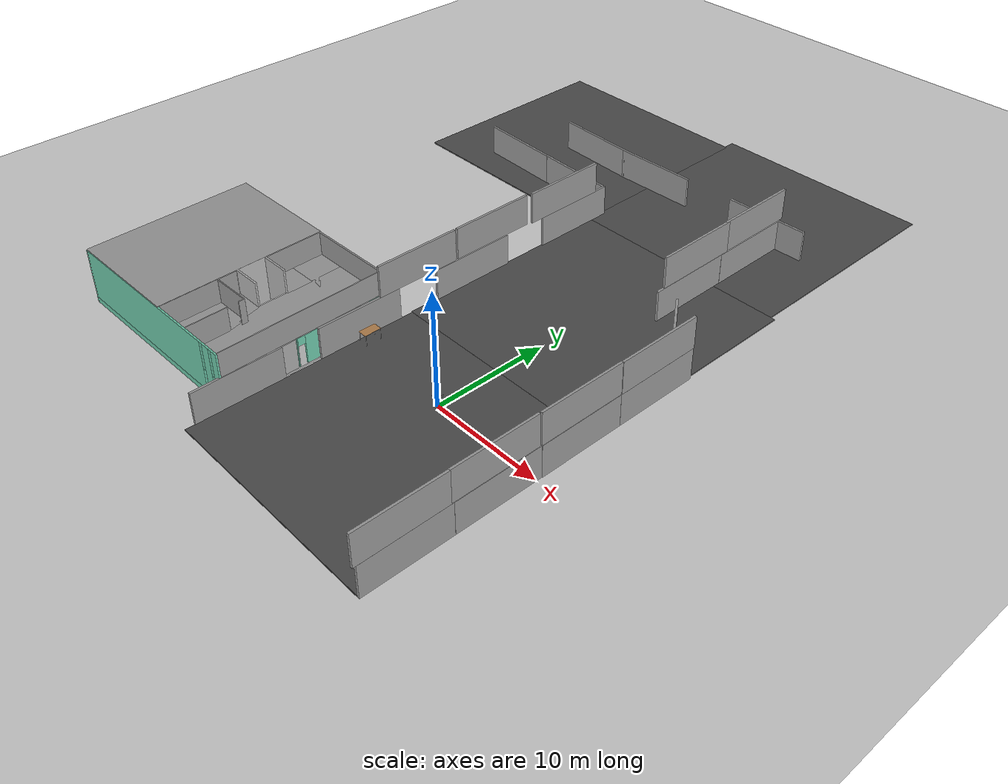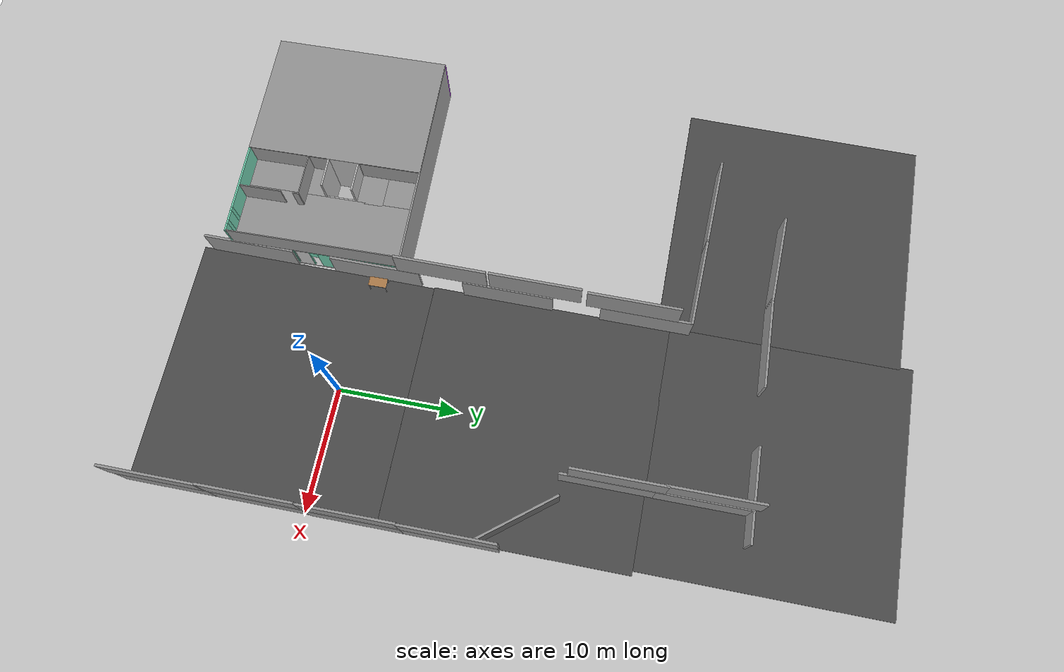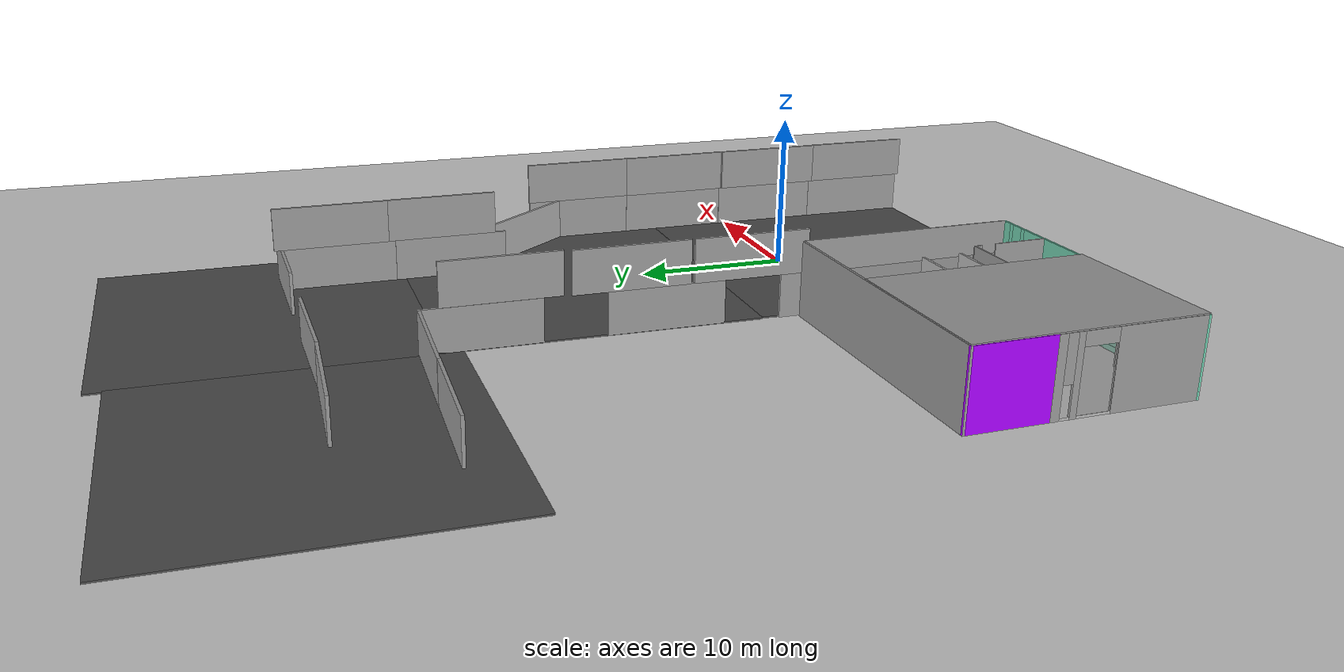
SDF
<sdf version="1.6">
 <world name="default">
  <include><uri>model://maav_matrice</uri><pose>0 0 1 0 0 1.57</pose></include>
  <plugin name="ground_truth_plugin" filename="libground_truth_plugin.so"/>
  <light name="sun" type="directional">
   <pose>0 0 10 0 -0 0</pose>
   <diffuse>0.8 0.8 0.8 1</diffuse>
   <specular>0.2 0.2 0.2 1</specular>
   <attenuation>
    <range>1000</range>
    <constant>0.9</constant>
    <linear>0.01</linear>
    <quadratic>0.001</quadratic>
   </attenuation>
   <direction>-0.5 0.1 -0.9</direction>
  </light>
  <physics name="default_physics" default="0" type="ode">
   <ode>
    <solver>
     <type>quick</type>
     <iters>10</iters>
     <sor>1.3</sor>
     <use_dynamic_moi_rescaling>0</use_dynamic_moi_rescaling>
    </solver>
    <constraints>
     <cfm>0</cfm>
     <erp>0.2</erp>
     <contact_max_correcting_vel>100</contact_max_correcting_vel>
     <contact_surface_layer>0.001</contact_surface_layer>
    </constraints>
   </ode>
   <max_step_size>0.002</max_step_size>
   <real_time_factor>1</real_time_factor>
   <real_time_update_rate>500</real_time_update_rate>
  </physics>
  <gravity>0 0 -9.8066</gravity>
  <magnetic_field>6e-06 2.3e-05 -4.2e-05</magnetic_field>
  <atmosphere type="adiabatic"/>
  <scene><ambient>0.4 0.4 0.4 1</ambient><background>0.7 0.7 0.7 1</background><shadows>1</shadows></scene>
  <spherical_coordinates>
   <surface_model>EARTH_WGS84</surface_model>
   <latitude_deg>0</latitude_deg>
   <longitude_deg>0</longitude_deg>
   <elevation>0</elevation>
   <heading_deg>0</heading_deg>
  </spherical_coordinates>
  <model name="asphalt_plane">
   <static>1</static>
   <link name="link">
    <collision name="collision"><geometry><box><size>20 20 0.1</size></box></geometry></collision>
    <visual name="visual">
     <cast_shadows>0</cast_shadows>
     <geometry><box><size>20 20 0.1</size></box></geometry>
     <material>
      <script>
       <uri>model://asphalt_plane/materials/scripts</uri>
       <uri>model://asphalt_plane/materials/textures</uri>
       <name>vrc/asphalt</name>
      </script>
     </material>
    </visual>
   </link>
   <pose>0.016282 -4.35292 0 0 -0 0</pose>
  </model>
  <model name="ground_plane">
   <static>1</static>
   <link name="link">
    <collision name="collision">
     <geometry><plane><normal>0 0 1</normal><size>100 100</size></plane></geometry>
     <surface>
      <contact><collide_bitmask>65535</collide_bitmask></contact>
      <friction><ode><mu>100</mu><mu2>50</mu2></ode></friction>
     </surface>
    </collision>
    <visual name="visual">
     <cast_shadows>0</cast_shadows>
     <geometry><plane><normal>0 0 1</normal><size>100 100</size></plane></geometry>
     <material>
      <script><uri>file://media/materials/scripts/gazebo.material</uri><name>Gazebo/Grey</name></script>
     </material>
    </visual>
   </link>
   <pose>-1.27431 2.91806 0 0 -0 0</pose>
  </model>
  <model name="asphalt_plane_0">
   <static>1</static>
   <link name="link">
    <collision name="collision"><geometry><box><size>20 20 0.1</size></box></geometry></collision>
    <visual name="visual">
     <cast_shadows>0</cast_shadows>
     <geometry><box><size>20 20 0.1</size></box></geometry>
     <material>
      <script>
       <uri>model://asphalt_plane/materials/scripts</uri>
       <uri>model://asphalt_plane/materials/textures</uri>
       <name>vrc/asphalt</name>
      </script>
     </material>
    </visual>
   </link>
   <pose>-0.082642 15.648 0 0 -0 0</pose>
  </model>
  <model name="grey_wall">
   <static>1</static>
   <link name="link">
    <pose>0 0 1.4 0 -0 0</pose>
    <collision name="collision"><geometry><box><size>7.5 0.2 2.8</size></box></geometry></collision>
    <visual name="visual">
     <cast_shadows>0</cast_shadows>
     <geometry><box><size>7.5 0.2 2.8</size></box></geometry>
     <material>
      <script>
       <uri>model://grey_wall/materials/scripts</uri>
       <uri>model://grey_wall/materials/textures</uri>
       <name>vrc/grey_wall</name>
      </script>
     </material>
    </visual>
   </link>
   <pose>-10.0517 -9.79742 0 0 -0 1.5731</pose>
  </model>
  <model name="grey_wall_clone">
   <static>1</static>
   <link name="link">
    <pose>0 0 1.4 0 -0 0</pose>
    <collision name="collision"><geometry><box><size>7.5 0.2 2.8</size></box></geometry></collision>
    <visual name="visual">
     <cast_shadows>0</cast_shadows>
     <geometry><box><size>7.5 0.2 2.8</size></box></geometry>
     <material>
      <script>
       <uri>model://grey_wall/materials/scripts</uri>
       <uri>model://grey_wall/materials/textures</uri>
       <name>vrc/grey_wall</name>
      </script>
     </material>
    </visual>
   </link>
   <pose>-10.103 0.859458 0 0 -0 1.5731</pose>
  </model>
  <model name="grey_wall_clone_0">
   <static>1</static>
   <link name="link">
    <pose>0 0 1.4 0 -0 0</pose>
    <collision name="collision"><geometry><box><size>7.5 0.2 2.8</size></box></geometry></collision>
    <visual name="visual">
     <cast_shadows>0</cast_shadows>
     <geometry><box><size>7.5 0.2 2.8</size></box></geometry>
     <material>
      <script>
       <uri>model://grey_wall/materials/scripts</uri>
       <uri>model://grey_wall/materials/textures</uri>
       <name>vrc/grey_wall</name>
      </script>
     </material>
    </visual>
   </link>
   <pose>-10.0463 11.9758 0 0 -0 1.5731</pose>
  </model>
  <model name="grey_wall_clone_1">
   <static>1</static>
   <link name="link">
    <pose>0 0 1.4 0 -0 0</pose>
    <collision name="collision"><geometry><box><size>7.5 0.2 2.8</size></box></geometry></collision>
    <visual name="visual">
     <cast_shadows>0</cast_shadows>
     <geometry><box><size>7.5 0.2 2.8</size></box></geometry>
     <material>
      <script>
       <uri>model://grey_wall/materials/scripts</uri>
       <uri>model://grey_wall/materials/textures</uri>
       <name>vrc/grey_wall</name>
      </script>
     </material>
    </visual>
   </link>
   <pose>-10.0443 23.4308 0 0 -0 1.5731</pose>
  </model>
  <model name="table">
   <static>1</static>
   <link name="link">
    <collision name="surface">
     <pose>0 0 1 0 -0 0</pose>
     <geometry><box><size>1.5 0.8 0.03</size></box></geometry>
     <surface><friction><ode><mu>0.6</mu><mu2>0.6</mu2></ode></friction></surface>
    </collision>
    <visual name="visual1">
     <pose>0 0 1 0 -0 0</pose>
     <geometry><box><size>1.5 0.8 0.03</size></box></geometry>
     <material>
      <script><uri>file://media/materials/scripts/gazebo.material</uri><name>Gazebo/Wood</name></script>
     </material>
    </visual>
    <collision name="front_left_leg">
     <pose>0.68 0.38 0.5 0 -0 0</pose>
     <geometry><cylinder><radius>0.02</radius><length>1</length></cylinder></geometry>
    </collision>
    <visual name="front_left_leg">
     <pose>0.68 0.38 0.5 0 -0 0</pose>
     <geometry><cylinder><radius>0.02</radius><length>1</length></cylinder></geometry>
     <material>
      <script><uri>file://media/materials/scripts/gazebo.material</uri><name>Gazebo/Grey</name></script>
     </material>
    </visual>
    <collision name="front_right_leg">
     <pose>0.68 -0.38 0.5 0 -0 0</pose>
     <geometry><cylinder><radius>0.02</radius><length>1</length></cylinder></geometry>
    </collision>
    <visual name="front_right_leg">
     <pose>0.68 -0.38 0.5 0 -0 0</pose>
     <geometry><cylinder><radius>0.02</radius><length>1</length></cylinder></geometry>
     <material>
      <script><uri>file://media/materials/scripts/gazebo.material</uri><name>Gazebo/Grey</name></script>
     </material>
    </visual>
    <collision name="back_right_leg">
     <pose>-0.68 -0.38 0.5 0 -0 0</pose>
     <geometry><cylinder><radius>0.02</radius><length>1</length></cylinder></geometry>
    </collision>
    <visual name="back_right_leg">
     <pose>-0.68 -0.38 0.5 0 -0 0</pose>
     <geometry><cylinder><radius>0.02</radius><length>1</length></cylinder></geometry>
     <material>
      <script><uri>file://media/materials/scripts/gazebo.material</uri><name>Gazebo/Grey</name></script>
     </material>
    </visual>
    <collision name="back_left_leg">
     <pose>-0.68 0.38 0.5 0 -0 0</pose>
     <geometry><cylinder><radius>0.02</radius><length>1</length></cylinder></geometry>
    </collision>
    <visual name="back_left_leg">
     <pose>-0.68 0.38 0.5 0 -0 0</pose>
     <geometry><cylinder><radius>0.02</radius><length>1</length></cylinder></geometry>
     <material>
      <script><uri>file://media/materials/scripts/gazebo.material</uri><name>Gazebo/Grey</name></script>
     </material>
    </visual>
   </link>
   <pose>-9.32133 1.09323 0.018125 -0.000255 -0.011983 -1.54953</pose>
  </model>
  <model name="grey_wall_clone_2">
   <static>1</static>
   <link name="link">
    <pose>0 0 1.4 0 -0 0</pose>
    <collision name="collision"><geometry><box><size>7.5 0.2 2.8</size></box></geometry></collision>
    <visual name="visual">
     <cast_shadows>0</cast_shadows>
     <geometry><box><size>7.5 0.2 2.8</size></box></geometry>
     <material>
      <script>
       <uri>model://grey_wall/materials/scripts</uri>
       <uri>model://grey_wall/materials/textures</uri>
       <name>vrc/grey_wall</name>
      </script>
     </material>
    </visual>
   </link>
   <pose>10.0233 -10.6229 0 0 -0 1.5731</pose>
  </model>
  <model name="grey_wall_clone_3">
   <static>1</static>
   <link name="link">
    <pose>0 0 1.4 0 -0 0</pose>
    <collision name="collision"><geometry><box><size>7.5 0.2 2.8</size></box></geometry></collision>
    <visual name="visual">
     <cast_shadows>0</cast_shadows>
     <geometry><box><size>7.5 0.2 2.8</size></box></geometry>
     <material>
      <script>
       <uri>model://grey_wall/materials/scripts</uri>
       <uri>model://grey_wall/materials/textures</uri>
       <name>vrc/grey_wall</name>
      </script>
     </material>
    </visual>
   </link>
   <pose>10.0149 -3.17281 0 0 -0 1.5731</pose>
  </model>
  <model name="grey_wall_clone_4">
   <static>1</static>
   <link name="link">
    <pose>0 0 1.4 0 -0 0</pose>
    <collision name="collision"><geometry><box><size>7.5 0.2 2.8</size></box></geometry></collision>
    <visual name="visual">
     <cast_shadows>0</cast_shadows>
     <geometry><box><size>7.5 0.2 2.8</size></box></geometry>
     <material>
      <script>
       <uri>model://grey_wall/materials/scripts</uri>
       <uri>model://grey_wall/materials/textures</uri>
       <name>vrc/grey_wall</name>
      </script>
     </material>
    </visual>
   </link>
   <pose>10.0341 4.23621 0 0 -0 1.5731</pose>
  </model>
  <model name="grey_wall_clone_5">
   <static>1</static>
   <link name="link">
    <pose>0 0 1.4 0 -0 0</pose>
    <collision name="collision"><geometry><box><size>7.5 0.2 2.8</size></box></geometry></collision>
    <visual name="visual">
     <cast_shadows>0</cast_shadows>
     <geometry><box><size>7.5 0.2 2.8</size></box></geometry>
     <material>
      <script>
       <uri>model://grey_wall/materials/scripts</uri>
       <uri>model://grey_wall/materials/textures</uri>
       <name>vrc/grey_wall</name>
      </script>
     </material>
    </visual>
   </link>
   <pose>10.0238 11.678 0 0 -0 1.5731</pose>
  </model>
  <model name="grey_wall_clone_7">
   <static>1</static>
   <link name="link">
    <pose>0 0 1.4 0 -0 0</pose>
    <collision name="collision"><geometry><box><size>7.5 0.2 2.8</size></box></geometry></collision>
    <visual name="visual">
     <cast_shadows>0</cast_shadows>
     <geometry><box><size>7.5 0.2 2.8</size></box></geometry>
     <material>
      <script>
       <uri>model://grey_wall/materials/scripts</uri>
       <uri>model://grey_wall/materials/textures</uri>
       <name>vrc/grey_wall</name>
      </script>
     </material>
    </visual>
   </link>
   <pose>3.69755 22.521 0 0 -0 1.5731</pose>
  </model>
  <model name="grey_wall_clone_5_clone">
   <static>1</static>
   <link name="link">
    <pose>0 0 1.4 0 -0 0</pose>
    <collision name="collision"><geometry><box><size>7.5 0.2 2.8</size></box></geometry></collision>
    <visual name="visual">
     <cast_shadows>0</cast_shadows>
     <geometry><box><size>7.5 0.2 2.8</size></box></geometry>
     <material>
      <script>
       <uri>model://grey_wall/materials/scripts</uri>
       <uri>model://grey_wall/materials/textures</uri>
       <name>vrc/grey_wall</name>
      </script>
     </material>
    </visual>
   </link>
   <pose>7.6586 16.1854 0 0 -0 2.23465</pose>
  </model>
  <model name="asphalt_plane_0_clone">
   <static>1</static>
   <link name="link">
    <collision name="collision"><geometry><box><size>20 20 0.1</size></box></geometry></collision>
    <visual name="visual">
     <cast_shadows>0</cast_shadows>
     <geometry><box><size>20 20 0.1</size></box></geometry>
     <material>
      <script>
       <uri>model://asphalt_plane/materials/scripts</uri>
       <uri>model://asphalt_plane/materials/textures</uri>
       <name>vrc/asphalt</name>
      </script>
     </material>
    </visual>
   </link>
   <pose>-0.458998 35.5899 0 0 -0 0</pose>
  </model>
  <model name="grey_wall_clone_7_clone">
   <static>1</static>
   <link name="link">
    <pose>0 0 1.4 0 -0 0</pose>
    <collision name="collision"><geometry><box><size>7.5 0.2 2.8</size></box></geometry></collision>
    <visual name="visual">
     <cast_shadows>0</cast_shadows>
     <geometry><box><size>7.5 0.2 2.8</size></box></geometry>
     <material>
      <script>
       <uri>model://grey_wall/materials/scripts</uri>
       <uri>model://grey_wall/materials/textures</uri>
       <name>vrc/grey_wall</name>
      </script>
     </material>
    </visual>
   </link>
   <pose>3.6938 30.0007 0 0 -0 1.5731</pose>
  </model>
  <model name="grey_wall_clone_7_clone_0">
   <static>1</static>
   <link name="link">
    <pose>0 0 1.4 0 -0 0</pose>
    <collision name="collision"><geometry><box><size>7.5 0.2 2.8</size></box></geometry></collision>
    <visual name="visual">
     <cast_shadows>0</cast_shadows>
     <geometry><box><size>7.5 0.2 2.8</size></box></geometry>
     <material>
      <script>
       <uri>model://grey_wall/materials/scripts</uri>
       <uri>model://grey_wall/materials/textures</uri>
       <name>vrc/grey_wall</name>
      </script>
     </material>
    </visual>
   </link>
   <pose>-13.7551 27.2191 0 0 -0 3.10768</pose>
  </model>
  <model name="grey_wall_clone_7_clone_1">
   <static>1</static>
   <link name="link">
    <pose>0 0 1.4 0 -0 0</pose>
    <collision name="collision"><geometry><box><size>7.5 0.2 2.8</size></box></geometry></collision>
    <visual name="visual">
     <cast_shadows>0</cast_shadows>
     <geometry><box><size>7.5 0.2 2.8</size></box></geometry>
     <material>
      <script>
       <uri>model://grey_wall/materials/scripts</uri>
       <uri>model://grey_wall/materials/textures</uri>
       <name>vrc/grey_wall</name>
      </script>
     </material>
    </visual>
   </link>
   <pose>2.50939 33.6742 0 0 -0 0.030482</pose>
  </model>
  <model name="grey_wall_clone_7_clone_1_clone">
   <static>1</static>
   <link name="link">
    <pose>0 0 1.4 0 -0 0</pose>
    <collision name="collision"><geometry><box><size>7.5 0.2 2.8</size></box></geometry></collision>
    <visual name="visual">
     <cast_shadows>0</cast_shadows>
     <geometry><box><size>7.5 0.2 2.8</size></box></geometry>
     <material>
      <script>
       <uri>model://grey_wall/materials/scripts</uri>
       <uri>model://grey_wall/materials/textures</uri>
       <name>vrc/grey_wall</name>
      </script>
     </material>
    </visual>
   </link>
   <pose>-9.64453 33.3043 0 0 -0 0.030482</pose>
  </model>
  <model name="asphalt_plane_0_clone_clone">
   <static>1</static>
   <link name="link">
    <collision name="collision"><geometry><box><size>20 20 0.1</size></box></geometry></collision>
    <visual name="visual">
     <cast_shadows>0</cast_shadows>
     <geometry><box><size>20 20 0.1</size></box></geometry>
     <material>
      <script>
       <uri>model://asphalt_plane/materials/scripts</uri>
       <uri>model://asphalt_plane/materials/textures</uri>
       <name>vrc/asphalt</name>
      </script>
     </material>
    </visual>
   </link>
   <pose>-20.2703 34.5479 0 0 -0 0</pose>
  </model>
  <model name="grey_wall_clone_7_clone_0_clone">
   <static>1</static>
   <link name="link">
    <pose>0 0 1.4 0 -0 0</pose>
    <collision name="collision"><geometry><box><size>7.5 0.2 2.8</size></box></geometry></collision>
    <visual name="visual">
     <cast_shadows>0</cast_shadows>
     <geometry><box><size>7.5 0.2 2.8</size></box></geometry>
     <material>
      <script>
       <uri>model://grey_wall/materials/scripts</uri>
       <uri>model://grey_wall/materials/textures</uri>
       <name>vrc/grey_wall</name>
      </script>
     </material>
    </visual>
   </link>
   <pose>-16.9368 33.3221 0 0 -0 3.10768</pose>
  </model>
  <model name="grey_wall_clone_7_clone_0_clone_0">
   <static>1</static>
   <link name="link">
    <pose>0 0 1.4 0 -0 0</pose>
    <collision name="collision"><geometry><box><size>7.5 0.2 2.8</size></box></geometry></collision>
    <visual name="visual">
     <cast_shadows>0</cast_shadows>
     <geometry><box><size>7.5 0.2 2.8</size></box></geometry>
     <material>
      <script>
       <uri>model://grey_wall/materials/scripts</uri>
       <uri>model://grey_wall/materials/textures</uri>
       <name>vrc/grey_wall</name>
      </script>
     </material>
    </visual>
   </link>
   <pose>-21.0764 27.4472 0 0 -0 3.10768</pose>
  </model>
  <model name="osrf_elevator">
   <link name="Wall_0">
    <pose>-7.17647 0.013004 0 0 -0 1.57174</pose>
    <visual name="Wall_0_Visual_0">
     <meta><layer>0</layer></meta>
     <pose>-8.72596 0 2.4385 0 -0 0</pose>
     <geometry><box><size>0.663656 0.15 4.877</size></box></geometry>
     <material>
      <script><uri>file://media/materials/scripts/gazebo.material</uri><name>Gazebo/Grey</name></script>
      <ambient>0.435294 0.796078 0.67451 1</ambient>
     </material>
    </visual>
    <collision name="Wall_0_Collision_0">
     <geometry><box><size>0.663656 0.15 4.877</size></box></geometry>
     <pose>-8.72596 0 2.4385 0 -0 0</pose>
    </collision>
    <visual name="Wall_0_Visual_1">
     <meta><layer>0</layer></meta>
     <pose>0.331828 0 0.25 0 -0 0</pose>
     <geometry><box><size>17.4519 0.15 0.5</size></box></geometry>
     <material>
      <script><uri>file://media/materials/scripts/gazebo.material</uri><name>Gazebo/Grey</name></script>
      <ambient>0.435294 0.796078 0.67451 1</ambient>
     </material>
    </visual>
    <collision name="Wall_0_Collision_1">
     <geometry><box><size>17.4519 0.15 0.5</size></box></geometry>
     <pose>0.331828 0 0.25 0 -0 0</pose>
    </collision>
    <visual name="Wall_0_Visual_2">
     <meta><layer>0</layer></meta>
     <pose>-7.67281 0 2.6885 0 -0 0</pose>
     <geometry><box><size>0.816657 0.15 4.377</size></box></geometry>
     <material>
      <script><uri>file://media/materials/scripts/gazebo.material</uri><name>Gazebo/Grey</name></script>
      <ambient>0.435294 0.796078 0.67451 1</ambient>
     </material>
    </visual>
    <collision name="Wall_0_Collision_2">
     <geometry><box><size>0.816657 0.15 4.377</size></box></geometry>
     <pose>-7.67281 0 2.6885 0 -0 0</pose>
    </collision>
    <visual name="Wall_0_Visual_3">
     <meta><layer>0</layer></meta>
     <pose>1.05709 0 2.6885 0 -0 0</pose>
     <geometry><box><size>16.0014 0.15 4.377</size></box></geometry>
     <material>
      <script><uri>file://media/materials/scripts/gazebo.material</uri><name>Gazebo/Grey</name></script>
      <ambient>0.435294 0.796078 0.67451 1</ambient>
     </material>
    </visual>
    <collision name="Wall_0_Collision_3">
     <geometry><box><size>16.0014 0.15 4.377</size></box></geometry>
     <pose>1.05709 0 2.6885 0 -0 0</pose>
    </collision>
    <visual name="Wall_0_Visual_4">
     <meta><layer>0</layer></meta>
     <pose>-8.23763 0 3.6885 0 -0 0</pose>
     <geometry><box><size>0.313 0.15 2.377</size></box></geometry>
     <material>
      <script><uri>file://media/materials/scripts/gazebo.material</uri><name>Gazebo/Grey</name></script>
      <ambient>0.435294 0.796078 0.67451 1</ambient>
     </material>
    </visual>
    <collision name="Wall_0_Collision_4">
     <geometry><box><size>0.313 0.15 2.377</size></box></geometry>
     <pose>-8.23763 0 3.6885 0 -0 0</pose>
    </collision>
    <visual name="Wall_0_Visual_5">
     <meta><layer>0</layer></meta>
     <pose>-7.10405 0 3.6885 0 -0 0</pose>
     <geometry><box><size>0.320861 0.15 2.377</size></box></geometry>
     <material>
      <script><uri>file://media/materials/scripts/gazebo.material</uri><name>Gazebo/Grey</name></script>
      <ambient>0.435294 0.796078 0.67451 1</ambient>
     </material>
    </visual>
    <collision name="Wall_0_Collision_5">
     <geometry><box><size>0.320861 0.15 2.377</size></box></geometry>
     <pose>-7.10405 0 3.6885 0 -0 0</pose>
    </collision>
   </link>
   <link name="Wall_10">
    <pose>3.11003 -4.9485 0 0 -0 0</pose>
    <visual name="Wall_10_Visual_0">
     <meta><layer>0</layer></meta>
     <pose>-1.73626 0 1.3715 0 -0 0</pose>
     <geometry><box><size>4.52747 0.15 2.743</size></box></geometry>
     <material>
      <script><uri>file://media/materials/scripts/gazebo.material</uri><name>Gazebo/Grey</name></script>
      <ambient>0 0.666667 0 1</ambient>
     </material>
    </visual>
    <collision name="Wall_10_Collision_0">
     <geometry><box><size>4.52747 0.15 2.743</size></box></geometry>
     <pose>-1.73626 0 1.3715 0 -0 0</pose>
    </collision>
    <visual name="Wall_10_Visual_1">
     <meta><layer>0</layer></meta>
     <pose>2.58694 0 1.3715 0 -0 0</pose>
     <geometry><box><size>2.82611 0.15 2.743</size></box></geometry>
     <material>
      <script><uri>file://media/materials/scripts/gazebo.material</uri><name>Gazebo/Grey</name></script>
      <ambient>0 0.666667 0 1</ambient>
     </material>
    </visual>
    <collision name="Wall_10_Collision_1">
     <geometry><box><size>2.82611 0.15 2.743</size></box></geometry>
     <pose>2.58694 0 1.3715 0 -0 0</pose>
    </collision>
    <visual name="Wall_10_Visual_2">
     <meta><layer>0</layer></meta>
     <pose>0.85068 0 2.3715 0 -0 0</pose>
     <geometry><box><size>0.646413 0.15 0.743</size></box></geometry>
     <material>
      <script><uri>file://media/materials/scripts/gazebo.material</uri><name>Gazebo/Grey</name></script>
      <ambient>0 0.666667 0 1</ambient>
     </material>
    </visual>
    <collision name="Wall_10_Collision_2">
     <geometry><box><size>0.646413 0.15 0.743</size></box></geometry>
     <pose>0.85068 0 2.3715 0 -0 0</pose>
    </collision>
   </link>
   <link name="Wall_14">
    <pose>1.83803 -6.9775 0 0 -0 1.5708</pose>
    <visual name="Wall_14_Visual_0">
     <meta><layer>0</layer></meta>
     <pose>-0.387674 0 1.3715 0 -0 0</pose>
     <geometry><box><size>3.41138 0.15 2.743</size></box></geometry>
     <material>
      <script><uri>file://media/materials/scripts/gazebo.material</uri><name>Gazebo/Grey</name></script>
      <ambient>1 1 1 1</ambient>
     </material>
    </visual>
    <collision name="Wall_14_Collision_0">
     <geometry><box><size>3.41138 0.15 2.743</size></box></geometry>
     <pose>-0.387674 0 1.3715 0 -0 0</pose>
    </collision>
    <visual name="Wall_14_Visual_1">
     <meta><layer>0</layer></meta>
     <pose>2.00133 0 1.3715 0 -0 0</pose>
     <geometry><box><size>0.184063 0.15 2.743</size></box></geometry>
     <material>
      <script><uri>file://media/materials/scripts/gazebo.material</uri><name>Gazebo/Grey</name></script>
      <ambient>1 1 1 1</ambient>
     </material>
    </visual>
    <collision name="Wall_14_Collision_1">
     <geometry><box><size>0.184063 0.15 2.743</size></box></geometry>
     <pose>2.00133 0 1.3715 0 -0 0</pose>
    </collision>
    <visual name="Wall_14_Visual_2">
     <meta><layer>0</layer></meta>
     <pose>1.61366 0 2.3715 0 -0 0</pose>
     <geometry><box><size>0.591285 0.15 0.743</size></box></geometry>
     <material>
      <script><uri>file://media/materials/scripts/gazebo.material</uri><name>Gazebo/Grey</name></script>
      <ambient>1 1 1 1</ambient>
     </material>
    </visual>
    <collision name="Wall_14_Collision_2">
     <geometry><box><size>0.591285 0.15 0.743</size></box></geometry>
     <pose>1.61366 0 2.3715 0 -0 0</pose>
    </collision>
   </link>
   <link name="Wall_16">
    <collision name="Wall_16_Collision">
     <geometry><box><size>5.12727 0.15 2.743</size></box></geometry>
     <pose>0 0 1.3715 0 -0 0</pose>
    </collision>
    <visual name="Wall_16_Visual">
     <meta><layer>0</layer></meta>
     <pose>0 0 1.3715 0 -0 0</pose>
     <geometry><box><size>5.12727 0.15 2.743</size></box></geometry>
     <material>
      <script><uri>file://media/materials/scripts/gazebo.material</uri><name>Gazebo/Grey</name></script>
      <ambient>1 1 1 1</ambient>
     </material>
    </visual>
    <pose>-4.68247 -1.4425 0 0 -0 0</pose>
   </link>
   <link name="Wall_17">
    <pose>-2.19097 -3.185 0 0 0 -1.56907</pose>
    <visual name="Wall_17_Visual_0">
     <meta><layer>0</layer></meta>
     <pose>-1.22855 0 1.3715 0 -0 0</pose>
     <geometry><box><size>1.17851 0.15 2.743</size></box></geometry>
     <material>
      <script><uri>file://media/materials/scripts/gazebo.material</uri><name>Gazebo/Grey</name></script>
      <ambient>1 1 1 1</ambient>
     </material>
    </visual>
    <collision name="Wall_17_Collision_0">
     <geometry><box><size>1.17851 0.15 2.743</size></box></geometry>
     <pose>-1.22855 0 1.3715 0 -0 0</pose>
    </collision>
    <visual name="Wall_17_Visual_1">
     <meta><layer>0</layer></meta>
     <pose>0.886237 0 1.3715 0 -0 0</pose>
     <geometry><box><size>1.86314 0.15 2.743</size></box></geometry>
     <material>
      <script><uri>file://media/materials/scripts/gazebo.material</uri><name>Gazebo/Grey</name></script>
      <ambient>1 1 1 1</ambient>
     </material>
    </visual>
    <collision name="Wall_17_Collision_1">
     <geometry><box><size>1.86314 0.15 2.743</size></box></geometry>
     <pose>0.886237 0 1.3715 0 -0 0</pose>
    </collision>
    <visual name="Wall_17_Visual_2">
     <meta><layer>0</layer></meta>
     <pose>1.18873 0 1.3715 0 -0 0</pose>
     <geometry><box><size>1.25815 0.15 2.743</size></box></geometry>
     <material>
      <script><uri>file://media/materials/scripts/gazebo.material</uri><name>Gazebo/Grey</name></script>
      <ambient>1 1 1 1</ambient>
     </material>
    </visual>
    <collision name="Wall_17_Collision_2">
     <geometry><box><size>1.25815 0.15 2.743</size></box></geometry>
     <pose>1.18873 0 1.3715 0 -0 0</pose>
    </collision>
    <visual name="Wall_17_Visual_3">
     <meta><layer>0</layer></meta>
     <pose>-0.345304 0 2.3715 0 -0 0</pose>
     <geometry><box><size>0.587991 0.15 0.743</size></box></geometry>
     <material>
      <script><uri>file://media/materials/scripts/gazebo.material</uri><name>Gazebo/Grey</name></script>
      <ambient>1 1 1 1</ambient>
     </material>
    </visual>
    <collision name="Wall_17_Collision_3">
     <geometry><box><size>0.587991 0.15 0.743</size></box></geometry>
     <pose>-0.345304 0 2.3715 0 -0 0</pose>
    </collision>
   </link>
   <link name="Wall_18">
    <collision name="Wall_18_Collision">
     <geometry><box><size>5 0.15 2.743</size></box></geometry>
     <pose>0 0 1.3715 0 -0 0</pose>
    </collision>
    <visual name="Wall_18_Visual">
     <meta><layer>0</layer></meta>
     <pose>0 0 1.3715 0 -0 0</pose>
     <geometry><box><size>5 0.15 2.743</size></box></geometry>
     <material>
      <script><uri>file://media/materials/scripts/gazebo.material</uri><name>Gazebo/Grey</name></script>
      <ambient>1 1 1 1</ambient>
     </material>
    </visual>
    <pose>-4.61297 -4.9275 0 0 -0 3.14159</pose>
   </link>
   <link name="Wall_20">
    <collision name="Wall_20_Collision">
     <geometry><box><size>2.88731 0.15 2.743</size></box></geometry>
     <pose>0 0 1.3715 0 -0 0</pose>
    </collision>
    <visual name="Wall_20_Visual">
     <meta><layer>0</layer></meta>
     <pose>0 0 1.3715 0 -0 0</pose>
     <geometry><box><size>2.88731 0.15 2.743</size></box></geometry>
     <material>
      <script><uri>file://media/materials/scripts/gazebo.material</uri><name>Gazebo/Grey</name></script>
      <ambient>1 1 1 1</ambient>
     </material>
    </visual>
    <pose>5.74253 1.037 0 0 0 -3.1383</pose>
   </link>
   <link name="Wall_21">
    <pose>4.37403 -1.8925 0 0 0 -1.5708</pose>
    <visual name="Wall_21_Visual_0">
     <meta><layer>0</layer></meta>
     <pose>-2.34405 0 1.3715 0 -0 0</pose>
     <geometry><box><size>1.3119 0.15 2.743</size></box></geometry>
     <material>
      <script><uri>file://media/materials/scripts/gazebo.material</uri><name>Gazebo/Grey</name></script>
      <ambient>1 1 1 1</ambient>
     </material>
    </visual>
    <collision name="Wall_21_Collision_0">
     <geometry><box><size>1.3119 0.15 2.743</size></box></geometry>
     <pose>-2.34405 0 1.3715 0 -0 0</pose>
    </collision>
    <visual name="Wall_21_Visual_1">
     <meta><layer>0</layer></meta>
     <pose>-0.970323 0 1.3715 0 -0 0</pose>
     <geometry><box><size>0.213619 0.15 2.743</size></box></geometry>
     <material>
      <script><uri>file://media/materials/scripts/gazebo.material</uri><name>Gazebo/Grey</name></script>
      <ambient>1 1 1 1</ambient>
     </material>
    </visual>
    <collision name="Wall_21_Collision_1">
     <geometry><box><size>0.213619 0.15 2.743</size></box></geometry>
     <pose>-0.970323 0 1.3715 0 -0 0</pose>
    </collision>
    <visual name="Wall_21_Visual_2">
     <meta><layer>0</layer></meta>
     <pose>0.938748 0 1.3715 0 -0 0</pose>
     <geometry><box><size>2.36558 0.15 2.743</size></box></geometry>
     <material>
      <script><uri>file://media/materials/scripts/gazebo.material</uri><name>Gazebo/Grey</name></script>
      <ambient>1 1 1 1</ambient>
     </material>
    </visual>
    <collision name="Wall_21_Collision_2">
     <geometry><box><size>2.36558 0.15 2.743</size></box></geometry>
     <pose>0.938748 0 1.3715 0 -0 0</pose>
    </collision>
    <visual name="Wall_21_Visual_3">
     <meta><layer>0</layer></meta>
     <pose>2.89346 0 1.3715 0 -0 0</pose>
     <geometry><box><size>0.213086 0.15 2.743</size></box></geometry>
     <material>
      <script><uri>file://media/materials/scripts/gazebo.material</uri><name>Gazebo/Grey</name></script>
      <ambient>1 1 1 1</ambient>
     </material>
    </visual>
    <collision name="Wall_21_Collision_3">
     <geometry><box><size>0.213086 0.15 2.743</size></box></geometry>
     <pose>2.89346 0 1.3715 0 -0 0</pose>
    </collision>
    <visual name="Wall_21_Visual_4">
     <meta><layer>0</layer></meta>
     <pose>-1.38262 0 2.3715 0 -0 0</pose>
     <geometry><box><size>0.610969 0.15 0.743</size></box></geometry>
     <material>
      <script><uri>file://media/materials/scripts/gazebo.material</uri><name>Gazebo/Grey</name></script>
      <ambient>1 1 1 1</ambient>
     </material>
    </visual>
    <collision name="Wall_21_Collision_4">
     <geometry><box><size>0.610969 0.15 0.743</size></box></geometry>
     <pose>-1.38262 0 2.3715 0 -0 0</pose>
    </collision>
    <visual name="Wall_21_Visual_5">
     <meta><layer>0</layer></meta>
     <pose>-0.553779 0 2.3715 0 -0 0</pose>
     <geometry><box><size>0.61947 0.15 0.743</size></box></geometry>
     <material>
      <script><uri>file://media/materials/scripts/gazebo.material</uri><name>Gazebo/Grey</name></script>
      <ambient>1 1 1 1</ambient>
     </material>
    </visual>
    <collision name="Wall_21_Collision_5">
     <geometry><box><size>0.61947 0.15 0.743</size></box></geometry>
     <pose>-0.553779 0 2.3715 0 -0 0</pose>
    </collision>
    <visual name="Wall_21_Visual_6">
     <meta><layer>0</layer></meta>
     <pose>2.45423 0 2.3715 0 -0 0</pose>
     <geometry><box><size>0.665375 0.15 0.743</size></box></geometry>
     <material>
      <script><uri>file://media/materials/scripts/gazebo.material</uri><name>Gazebo/Grey</name></script>
      <ambient>1 1 1 1</ambient>
     </material>
    </visual>
    <collision name="Wall_21_Collision_6">
     <geometry><box><size>0.665375 0.15 0.743</size></box></geometry>
     <pose>2.45423 0 2.3715 0 -0 0</pose>
    </collision>
   </link>
   <link name="Wall_23">
    <collision name="Wall_23_Collision">
     <geometry><box><size>2.75 0.15 2.743</size></box></geometry>
     <pose>0 0 1.3715 0 -0 0</pose>
    </collision>
    <visual name="Wall_23_Visual">
     <meta><layer>0</layer></meta>
     <pose>0 0 1.3715 0 -0 0</pose>
     <geometry><box><size>2.75 0.15 2.743</size></box></geometry>
     <material>
      <script><uri>file://media/materials/scripts/gazebo.material</uri><name>Gazebo/Grey</name></script>
      <ambient>1 1 1 1</ambient>
     </material>
    </visual>
    <pose>5.74203 -2.9565 0 0 -0 0</pose>
   </link>
   <link name="Wall_25">
    <collision name="Wall_25_Collision">
     <geometry><box><size>2.75 0.15 2.743</size></box></geometry>
     <pose>0 0 1.3715 0 -0 0</pose>
    </collision>
    <visual name="Wall_25_Visual">
     <meta><layer>0</layer></meta>
     <pose>0 0 1.3715 0 -0 0</pose>
     <geometry><box><size>2.75 0.15 2.743</size></box></geometry>
     <material>
      <script><uri>file://media/materials/scripts/gazebo.material</uri><name>Gazebo/Grey</name></script>
      <ambient>1 1 1 1</ambient>
     </material>
    </visual>
    <pose>5.76203 -0.932496 0 0 -0 0</pose>
   </link>
   <link name="Wall_27">
    <collision name="Wall_27_Collision">
     <geometry><box><size>4 0.15 2.743</size></box></geometry>
     <pose>0 0 1.3715 0 -0 0</pose>
    </collision>
    <visual name="Wall_27_Visual">
     <meta><layer>0</layer></meta>
     <pose>0 0 1.3715 0 -0 0</pose>
     <geometry><box><size>4 0.15 2.743</size></box></geometry>
     <material>
      <script><uri>file://media/materials/scripts/gazebo.material</uri><name>Gazebo/Grey</name></script>
      <ambient>1 1 1 1</ambient>
     </material>
    </visual>
    <pose>4.75503 -7.0125 0 0 -0 1.5708</pose>
   </link>
   <link name="Wall_29">
    <collision name="Wall_29_Collision">
     <geometry><box><size>1.39187 0.15 4.877</size></box></geometry>
     <pose>0 0 2.4385 0 -0 0</pose>
    </collision>
    <visual name="Wall_29_Visual">
     <meta><layer>0</layer></meta>
     <pose>0 0 2.4385 0 -0 0</pose>
     <geometry><box><size>1.39187 0.15 4.877</size></box></geometry>
     <material>
      <script><uri>file://media/materials/scripts/gazebo.material</uri><name>Gazebo/Grey</name></script>
      <ambient>0.996078 0.47451 0.0196078 1</ambient>
     </material>
    </visual>
    <pose>-6.49697 4.1045 0 0 -0 0</pose>
   </link>
   <link name="Wall_30">
    <collision name="Wall_30_Collision">
     <geometry><box><size>3 0.15 4.877</size></box></geometry>
     <pose>0 0 2.4385 0 -0 0</pose>
    </collision>
    <visual name="Wall_30_Visual">
     <meta><layer>0</layer></meta>
     <pose>0 0 2.4385 0 -0 0</pose>
     <geometry><box><size>3 0.15 4.877</size></box></geometry>
     <material>
      <script><uri>file://media/materials/scripts/gazebo.material</uri><name>Gazebo/Grey</name></script>
      <ambient>1 1 1 1</ambient>
     </material>
    </visual>
    <pose>-5.87597 5.5295 0 0 -0 1.5708</pose>
   </link>
   <link name="Wall_31">
    <pose>-6.50397 6.9525 0 0 0 -3.13841</pose>
    <visual name="Wall_31_Visual_0">
     <meta><layer>0</layer></meta>
     <pose>-0.567544 0 2.4385 0 -0 0</pose>
     <geometry><box><size>0.271575 0.15 4.877</size></box></geometry>
     <material>
      <script><uri>file://media/materials/scripts/gazebo.material</uri><name>Gazebo/Grey</name></script>
      <ambient>1 1 1 1</ambient>
     </material>
    </visual>
    <collision name="Wall_31_Collision_0">
     <geometry><box><size>0.271575 0.15 4.877</size></box></geometry>
     <pose>-0.567544 0 2.4385 0 -0 0</pose>
    </collision>
    <visual name="Wall_31_Visual_1">
     <meta><layer>0</layer></meta>
     <pose>0.441678 0 2.4385 0 -0 0</pose>
     <geometry><box><size>0.523307 0.15 4.877</size></box></geometry>
     <material>
      <script><uri>file://media/materials/scripts/gazebo.material</uri><name>Gazebo/Grey</name></script>
      <ambient>1 1 1 1</ambient>
     </material>
    </visual>
    <collision name="Wall_31_Collision_1">
     <geometry><box><size>0.523307 0.15 4.877</size></box></geometry>
     <pose>0.441678 0 2.4385 0 -0 0</pose>
    </collision>
    <visual name="Wall_31_Visual_3">
     <meta><layer>0</layer></meta>
     <pose>-0.125866 0 3.4385 0 -0 0</pose>
     <geometry><box><size>0.611781 0.15 2.877</size></box></geometry>
     <material>
      <script><uri>file://media/materials/scripts/gazebo.material</uri><name>Gazebo/Grey</name></script>
      <ambient>1 1 1 1</ambient>
     </material>
    </visual>
    <collision name="Wall_31_Collision_3">
     <geometry><box><size>0.611781 0.15 2.877</size></box></geometry>
     <pose>-0.125866 0 3.4385 0 -0 0</pose>
    </collision>
   </link>
   <link name="Wall_35">
    <pose>-2.50997 8.9955 0 0 -0 0</pose>
    <visual name="Wall_35_Visual_0">
     <meta><layer>0</layer></meta>
     <pose>-1.92197 0 2.4385 0 -0 0</pose>
     <geometry><box><size>5.65606 0.15 4.877</size></box></geometry>
     <material>
      <script><uri>file://media/materials/scripts/gazebo.material</uri><name>Gazebo/Grey</name></script>
      <ambient>1 1 1 1</ambient>
     </material>
    </visual>
    <collision name="Wall_35_Collision_0">
     <geometry><box><size>5.65606 0.15 4.877</size></box></geometry>
     <pose>-1.92197 0 2.4385 0 -0 0</pose>
    </collision>
    <visual name="Wall_35_Visual_1">
     <meta><layer>0</layer></meta>
     <pose>3.22541 0 2.4385 0 -0 0</pose>
     <geometry><box><size>0.406701 0.15 4.877</size></box></geometry>
     <material>
      <script><uri>file://media/materials/scripts/gazebo.material</uri><name>Gazebo/Grey</name></script>
      <ambient>1 1 1 1</ambient>
     </material>
    </visual>
    <collision name="Wall_35_Collision_1">
     <geometry><box><size>0.406701 0.15 4.877</size></box></geometry>
     <pose>3.22541 0 2.4385 0 -0 0</pose>
    </collision>
    <visual name="Wall_35_Visual_2">
     <meta><layer>0</layer></meta>
     <pose>4.40208 0 2.4385 0 -0 0</pose>
     <geometry><box><size>0.695843 0.15 4.877</size></box></geometry>
     <material>
      <script><uri>file://media/materials/scripts/gazebo.material</uri><name>Gazebo/Grey</name></script>
      <ambient>1 1 1 1</ambient>
     </material>
    </visual>
    <collision name="Wall_35_Collision_2">
     <geometry><box><size>0.695843 0.15 4.877</size></box></geometry>
     <pose>4.40208 0 2.4385 0 -0 0</pose>
    </collision>
    <visual name="Wall_35_Visual_5">
     <meta><layer>0</layer></meta>
     <pose>3.74146 0 3.4385 0 -0 0</pose>
     <geometry><box><size>0.625391 0.15 2.877</size></box></geometry>
     <material>
      <script><uri>file://media/materials/scripts/gazebo.material</uri><name>Gazebo/Grey</name></script>
      <ambient>1 1 1 1</ambient>
     </material>
    </visual>
    <collision name="Wall_35_Collision_5">
     <geometry><box><size>0.625391 0.15 2.877</size></box></geometry>
     <pose>3.74146 0 3.4385 0 -0 0</pose>
    </collision>
    <visual name="Wall_35_Visual_6">
     <meta><layer>0</layer></meta>
     <pose>1.96406 0 4.4385 0 -0 0</pose>
     <geometry><box><size>2.116 0.15 0.877</size></box></geometry>
     <material>
      <script><uri>file://media/materials/scripts/gazebo.material</uri><name>Gazebo/Grey</name></script>
      <ambient>1 1 1 1</ambient>
     </material>
    </visual>
    <collision name="Wall_35_Collision_6">
     <geometry><box><size>2.116 0.15 0.877</size></box></geometry>
     <pose>1.96406 0 4.4385 0 -0 0</pose>
    </collision>
   </link>
   <link name="Wall_36">
    <collision name="Wall_36_Collision">
     <geometry><box><size>5.17 0.15 4.877</size></box></geometry>
     <pose>0 0 2.4385 0 -0 0</pose>
    </collision>
    <visual name="Wall_36_Visual">
     <meta><layer>0</layer></meta>
     <pose>0 0 2.4385 0 -0 0</pose>
     <geometry><box><size>5.17 0.15 4.877</size></box></geometry>
     <material>
      <script><uri>file://media/materials/scripts/gazebo.material</uri><name>Gazebo/Grey</name></script>
      <ambient>0.666667 0 1 1</ambient>
     </material>
    </visual>
    <pose>4.67503 8.9955 0 0 -0 0</pose>
   </link>
   <link name="Wall_5">
    <collision name="Wall_5_Collision">
     <geometry><box><size>18.1152 0.15 4.877</size></box></geometry>
     <pose>0 0 2.4385 0 -0 0</pose>
    </collision>
    <visual name="Wall_5_Visual">
     <meta><layer>0</layer></meta>
     <pose>0 0 2.4385 0 -0 0</pose>
     <geometry><box><size>18.1152 0.15 4.877</size></box></geometry>
     <material>
      <script><uri>file://media/materials/scripts/gazebo.material</uri><name>Gazebo/Grey</name></script>
      <ambient>1 1 1 1</ambient>
     </material>
    </visual>
    <pose>7.18353 0.013004 0 0 0 -1.57096</pose>
   </link>
   <link name="Wall_6">
    <pose>0.007029 -8.9695 0 0 -0 3.14159</pose>
    <visual name="Wall_6_Visual_0">
     <meta><layer>0</layer></meta>
     <pose>-3.60425 0 1.365 0 -0 0</pose>
     <geometry><box><size>7.2915 0.15 2.73</size></box></geometry>
     <material>
      <script><uri>file://media/materials/scripts/gazebo.material</uri><name>Gazebo/Grey</name></script>
      <ambient>0.435294 0.796078 0.67451 1</ambient>
     </material>
    </visual>
    <collision name="Wall_6_Collision_0">
     <geometry><box><size>7.2915 0.15 2.73</size></box></geometry>
     <pose>-3.60425 0 1.365 0 -0 0</pose>
    </collision>
    <visual name="Wall_6_Visual_1">
     <meta><layer>0</layer></meta>
     <pose>0.726241 0 1.365 0 -0 0</pose>
     <geometry><box><size>0.056893 0.15 2.73</size></box></geometry>
     <material>
      <script><uri>file://media/materials/scripts/gazebo.material</uri><name>Gazebo/Grey</name></script>
      <ambient>0.435294 0.796078 0.67451 1</ambient>
     </material>
    </visual>
    <collision name="Wall_6_Collision_1">
     <geometry><box><size>0.056893 0.15 2.73</size></box></geometry>
     <pose>0.726241 0 1.365 0 -0 0</pose>
    </collision>
    <visual name="Wall_6_Visual_2">
     <meta><layer>0</layer></meta>
     <pose>2.65105 0 1.365 0 -0 0</pose>
     <geometry><box><size>1.19273 0.15 2.73</size></box></geometry>
     <material>
      <script><uri>file://media/materials/scripts/gazebo.material</uri><name>Gazebo/Grey</name></script>
      <ambient>0.435294 0.796078 0.67451 1</ambient>
     </material>
    </visual>
    <collision name="Wall_6_Collision_2">
     <geometry><box><size>1.19273 0.15 2.73</size></box></geometry>
     <pose>2.65105 0 1.365 0 -0 0</pose>
    </collision>
    <visual name="Wall_6_Visual_4">
     <meta><layer>0</layer></meta>
     <pose>5.24871 0 0.25 0 -0 0</pose>
     <geometry><box><size>4.00258 0.15 0.5</size></box></geometry>
     <material>
      <script><uri>file://media/materials/scripts/gazebo.material</uri><name>Gazebo/Grey</name></script>
      <ambient>0.435294 0.796078 0.67451 1</ambient>
     </material>
    </visual>
    <collision name="Wall_6_Collision_4">
     <geometry><box><size>4.00258 0.15 0.5</size></box></geometry>
     <pose>5.24871 0 0.25 0 -0 0</pose>
    </collision>
    <visual name="Wall_6_Visual_5">
     <meta><layer>0</layer></meta>
     <pose>4.0419 0 1.615 0 -0 0</pose>
     <geometry><box><size>0.828969 0.15 2.23</size></box></geometry>
     <material>
      <script><uri>file://media/materials/scripts/gazebo.material</uri><name>Gazebo/Grey</name></script>
      <ambient>0.435294 0.796078 0.67451 1</ambient>
     </material>
    </visual>
    <collision name="Wall_6_Collision_5">
     <geometry><box><size>0.828969 0.15 2.23</size></box></geometry>
     <pose>4.0419 0 1.615 0 -0 0</pose>
    </collision>
    <visual name="Wall_6_Visual_6">
     <meta><layer>0</layer></meta>
     <pose>5.18099 0 1.615 0 -0 0</pose>
     <geometry><box><size>0.819207 0.15 2.23</size></box></geometry>
     <material>
      <script><uri>file://media/materials/scripts/gazebo.material</uri><name>Gazebo/Grey</name></script>
      <ambient>0.435294 0.796078 0.67451 1</ambient>
     </material>
    </visual>
    <collision name="Wall_6_Collision_6">
     <geometry><box><size>0.819207 0.15 2.23</size></box></geometry>
     <pose>5.18099 0 1.615 0 -0 0</pose>
    </collision>
    <visual name="Wall_6_Visual_7">
     <meta><layer>0</layer></meta>
     <pose>6.58056 0 1.615 0 -0 0</pose>
     <geometry><box><size>1.33888 0.15 2.23</size></box></geometry>
     <material>
      <script><uri>file://media/materials/scripts/gazebo.material</uri><name>Gazebo/Grey</name></script>
      <ambient>0.435294 0.796078 0.67451 1</ambient>
     </material>
    </visual>
    <collision name="Wall_6_Collision_7">
     <geometry><box><size>1.33888 0.15 2.23</size></box></geometry>
     <pose>6.58056 0 1.615 0 -0 0</pose>
    </collision>
    <visual name="Wall_6_Visual_8">
     <meta><layer>0</layer></meta>
     <pose>0.369648 0 2.365 0 -0 0</pose>
     <geometry><box><size>0.656294 0.15 0.73</size></box></geometry>
     <material>
      <script><uri>file://media/materials/scripts/gazebo.material</uri><name>Gazebo/Grey</name></script>
      <ambient>0.435294 0.796078 0.67451 1</ambient>
     </material>
    </visual>
    <collision name="Wall_6_Collision_8">
     <geometry><box><size>0.656294 0.15 0.73</size></box></geometry>
     <pose>0.369648 0 2.365 0 -0 0</pose>
    </collision>
    <visual name="Wall_6_Visual_9">
     <meta><layer>0</layer></meta>
     <pose>3.43742 0 2.615 0 -0 0</pose>
     <geometry><box><size>0.38 0.15 0.23</size></box></geometry>
     <material>
      <script><uri>file://media/materials/scripts/gazebo.material</uri><name>Gazebo/Grey</name></script>
      <ambient>0.435294 0.796078 0.67451 1</ambient>
     </material>
    </visual>
    <collision name="Wall_6_Collision_9">
     <geometry><box><size>0.38 0.15 0.23</size></box></geometry>
     <pose>3.43742 0 2.615 0 -0 0</pose>
    </collision>
    <visual name="Wall_6_Visual_10">
     <meta><layer>0</layer></meta>
     <pose>4.61389 0 2.615 0 -0 0</pose>
     <geometry><box><size>0.315 0.15 0.23</size></box></geometry>
     <material>
      <script><uri>file://media/materials/scripts/gazebo.material</uri><name>Gazebo/Grey</name></script>
      <ambient>0.435294 0.796078 0.67451 1</ambient>
     </material>
    </visual>
    <collision name="Wall_6_Collision_10">
     <geometry><box><size>0.315 0.15 0.23</size></box></geometry>
     <pose>4.61389 0 2.615 0 -0 0</pose>
    </collision>
    <visual name="Wall_6_Visual_11">
     <meta><layer>0</layer></meta>
     <pose>5.75086 0 2.615 0 -0 0</pose>
     <geometry><box><size>0.320532 0.15 0.23</size></box></geometry>
     <material>
      <script><uri>file://media/materials/scripts/gazebo.material</uri><name>Gazebo/Grey</name></script>
      <ambient>0.435294 0.796078 0.67451 1</ambient>
     </material>
    </visual>
    <collision name="Wall_6_Collision_11">
     <geometry><box><size>0.320532 0.15 0.23</size></box></geometry>
     <pose>5.75086 0 2.615 0 -0 0</pose>
    </collision>
   </link>
   <link name="front_window">
    <pose>-1.42369 -8.99808 1.36421 0 -0 0</pose>
    <collision name="front_window_collision">
     <geometry><box><size>1.37422 0.034702 2.72768</size></box></geometry>
    </collision>
    <visual name="front_window_visual">
     <meta><layer>0</layer></meta>
     <geometry><box><size>1.37422 0.034702 2.72768</size></box></geometry>
     <material><script><name>Gazebo/GreyTransparent</name><uri>__default__</uri></script></material>
    </visual>
   </link>
   <link name="garage_door">
    <pose>-0.536243 9 2 0 -0 0</pose>
    <collision name="collision"><geometry><box><size>2.19515 0.034702 4</size></box></geometry></collision>
    <visual name="visual">
     <meta><layer>0</layer></meta>
     <geometry><box><size>2.19151 0.034702 4</size></box></geometry>
     <material><script><name>Gazebo/GreyTransparent</name><uri>__default__</uri></script></material>
    </visual>
   </link>
   <link name="ceiling1_part1">
    <pose>0.055266 -6.45681 2.76928 0 -0 0</pose>
    <collision name="collision"><geometry><box><size>14.4026 5.175 0.078</size></box></geometry></collision>
    <visual name="visual">
     <meta><layer>1</layer></meta>
     <geometry><box><size>14.4026 5.175 0.078</size></box></geometry>
     <material><script><name>Gazebo/Grey</name><uri>__default__</uri></script></material>
    </visual>
   </link>
   <link name="ceiling1_part2">
    <pose>-3.85568 -3.13263 2.76928 0 -0 0</pose>
    <collision name="collision"><geometry><box><size>6.64939 3.53076 0.078</size></box></geometry></collision>
    <visual name="visual">
     <meta><layer>1</layer></meta>
     <geometry><box><size>6.64939 3.53076 0.078</size></box></geometry>
     <material><script><name>Gazebo/Grey</name><uri>__default__</uri></script></material>
    </visual>
   </link>
   <link name="ceiling1_part3">
    <pose>5.71297 -1.93585 2.76928 0 -0 0</pose>
    <collision name="collision"><geometry><box><size>2.82725 6.08484 0.078</size></box></geometry></collision>
    <visual name="visual">
     <meta><layer>1</layer></meta>
     <geometry><box><size>2.82725 6.08484 0.078</size></box></geometry>
     <material><script><name>Gazebo/Grey</name><uri>__default__</uri></script></material>
    </visual>
   </link>
   <link name="ceiling1_part4">
    <pose>0 3.79823 4.91588 0 -0 0</pose>
    <collision name="collision"><geometry><box><size>14.4595 10.4662 0.078</size></box></geometry></collision>
    <visual name="visual">
     <meta><layer>1</layer></meta>
     <geometry><box><size>14.4595 10.4662 0.078</size></box></geometry>
     <material><script><name>Gazebo/Grey</name><uri>__default__</uri></script></material>
    </visual>
   </link>
   <link name="floor1_part5">
    <pose>-4.65046 -1.39728 3.85794 1.5708 -0 0</pose>
    <collision name="collision"><geometry><box><size>5.03711 2.0998 0.078</size></box></geometry></collision>
    <visual name="visual">
     <meta><layer>1</layer></meta>
     <geometry><box><size>5.03711 2.0998 0.078</size></box></geometry>
     <material><script><name>Gazebo/Grey</name><uri>__default__</uri></script></material>
    </visual>
   </link>
   <link name="floor1_part6">
    <pose>5.71783 1.06705 3.85828 1.5708 -0 0</pose>
    <collision name="collision"><geometry><box><size>2.83967 2.0998 0.078</size></box></geometry></collision>
    <visual name="visual">
     <meta><layer>1</layer></meta>
     <geometry><box><size>2.83967 2.0998 0.078</size></box></geometry>
     <material><script><name>Gazebo/Grey</name><uri>__default__</uri></script></material>
    </visual>
   </link>
   <link name="floor1_part7">
    <pose>2.39941 -1.39058 3.85828 1.5708 -0 0</pose>
    <collision name="collision"><geometry><box><size>9.43026 2.0998 0.078</size></box></geometry></collision>
    <visual name="visual">
     <meta><layer>1</layer></meta>
     <geometry><box><size>9.43026 2.0998 0.078</size></box></geometry>
     <material><script><name>Gazebo/Grey</name><uri>__default__</uri></script></material>
    </visual>
   </link>
   <link name="floor1_part8">
    <pose>0 -9 3.86461 1.5708 -0 0</pose>
    <collision name="collision"><geometry><box><size>14.2592 2.0998 0.078</size></box></geometry></collision>
    <visual name="visual">
     <meta><layer>1</layer></meta>
     <geometry><box><size>14.2592 2.0998 0.078</size></box></geometry>
     <material><script><name>Gazebo/Grey</name><uri>__default__</uri></script></material>
    </visual>
   </link>
   <link name="floor1_part9">
    <pose>-5.36806 -4.90906 3.85794 1.5708 -0 0</pose>
    <collision name="collision"><geometry><box><size>3.47446 2.0998 0.078</size></box></geometry></collision>
    <visual name="visual">
     <meta><layer>1</layer></meta>
     <geometry><box><size>3.47446 2.0998 0.078</size></box></geometry>
     <material><script><name>Gazebo/Grey</name><uri>__default__</uri></script></material>
    </visual>
   </link>
   <link name="floor1_part10">
    <pose>-2.39225 -4.89435 3.85794 1.5708 -0 0</pose>
    <collision name="collision"><geometry><box><size>0.519866 2.0998 0.078</size></box></geometry></collision>
    <visual name="visual">
     <meta><layer>1</layer></meta>
     <geometry><box><size>0.519866 2.0998 0.078</size></box></geometry>
     <material><script><name>Gazebo/Grey</name><uri>__default__</uri></script></material>
    </visual>
   </link>
   <link name="floor1_part11">
    <pose>-2.17305 -3.18058 3.85794 1.5708 0 -1.5708</pose>
    <collision name="collision"><geometry><box><size>3.4917 2.0998 0.078</size></box></geometry></collision>
    <visual name="visual">
     <meta><layer>1</layer></meta>
     <geometry><box><size>3.4917 2.0998 0.078</size></box></geometry>
     <material><script><name>Gazebo/Grey</name><uri>__default__</uri></script></material>
    </visual>
   </link>
   <link name="floor1_part12">
    <pose>3.22506 -2.66914 2.76928 0 -0 0</pose>
    <collision name="collision"><geometry><box><size>2.20229 2.60169 0.078</size></box></geometry></collision>
    <visual name="visual">
     <meta><layer>1</layer></meta>
     <geometry><box><size>2.20229 2.60169 0.078</size></box></geometry>
     <material><script><name>Gazebo/Grey</name><uri>__default__</uri></script></material>
    </visual>
   </link>
   <link name="ground_floor">
    <pose>0 0 0.075 0 -0 0</pose>
    <collision name="collision">
     <geometry><box><size>14.4 18.1 0.15</size></box></geometry>
     <surface><contact><collide_bitmask>1</collide_bitmask></contact></surface>
    </collision>
    <visual name="visual"><geometry><box><size>14.4 18.1 0.15</size></box></geometry></visual>
   </link>
   <link name="elevator_shaft">
    <pose>0.781821 -2.6219 0 0 0 -1.5708</pose>
    <collision name="shaft_wall1_collision">
     <pose>0 1.25 2.4774 0 -0 0</pose>
     <geometry><box><size>2.5 0.15 4.95479</size></box></geometry>
    </collision>
    <visual name="shaft_wall1_visual">
     <pose>0 1.25 2.4774 0 -0 0</pose>
     <geometry><box><size>2.5 0.15 4.95479</size></box></geometry>
    </visual>
    <collision name="shaft_wall2_collision">
     <pose>0 -1.25 2.4774 0 -0 0</pose>
     <geometry><box><size>2.5 0.15 4.95479</size></box></geometry>
    </collision>
    <visual name="shaft_wall2_visual">
     <pose>0 -1.25 2.4774 0 -0 0</pose>
     <geometry><box><size>2.5 0.15 4.95479</size></box></geometry>
    </visual>
    <collision name="shaft_wall3_collision">
     <pose>-1.25 0 2.4774 0 -0 0</pose>
     <geometry><box><size>0.15 2.7 4.95479</size></box></geometry>
    </collision>
    <visual name="shaft_wall3_visual">
     <pose>-1.25 0 2.4774 0 -0 0</pose>
     <geometry><box><size>0.15 2.7 4.95479</size></box></geometry>
    </visual>
    <collision name="floor0_collision">
     <pose>1.19 0 0.075 0 -0 0</pose>
     <geometry><box><size>0.12 2.5 0.15</size></box></geometry>
    </collision>
    <visual name="floor0_visual">
     <pose>1.19 0 0.075 0 -0 0</pose>
     <geometry><box><size>0.12 2.5 0.15</size></box></geometry>
    </visual>
    <collision name="floor1_collision">
     <pose>1.19 0 2.70825 0 -0 0</pose>
     <geometry><box><size>0.12 2.5 0.2</size></box></geometry>
    </collision>
    <visual name="floor1_visual">
     <pose>1.19 0 2.70825 0 -0 0</pose>
     <geometry><box><size>0.12 2.5 0.2</size></box></geometry>
    </visual>
   </link>
   <static>1</static>
   <pose>-19.2133 -4.15757 0 0 -0 1.59408</pose>
  </model>
  <model name="grey_wall_clone_2_clone">
   <static>1</static>
   <link name="link">
    <pose>0 0 1.4 0 -0 0</pose>
    <collision name="collision"><geometry><box><size>7.5 0.2 2.8</size></box></geometry></collision>
    <visual name="visual">
     <cast_shadows>0</cast_shadows>
     <geometry><box><size>7.5 0.2 2.8</size></box></geometry>
     <material>
      <script>
       <uri>model://grey_wall/materials/scripts</uri>
       <uri>model://grey_wall/materials/textures</uri>
       <name>vrc/grey_wall</name>
      </script>
     </material>
    </visual>
   </link>
   <pose>10.023 -10.8574 2.80072 0 -0 1.5731</pose>
  </model>
  <model name="grey_wall_clone_2_clone_clone">
   <static>1</static>
   <link name="link">
    <pose>0 0 1.4 0 -0 0</pose>
    <collision name="collision"><geometry><box><size>7.5 0.2 2.8</size></box></geometry></collision>
    <visual name="visual">
     <cast_shadows>0</cast_shadows>
     <geometry><box><size>7.5 0.2 2.8</size></box></geometry>
     <material>
      <script>
       <uri>model://grey_wall/materials/scripts</uri>
       <uri>model://grey_wall/materials/textures</uri>
       <name>vrc/grey_wall</name>
      </script>
     </material>
    </visual>
   </link>
   <pose>9.96798 -3.36649 2.80072 0 -0 1.5731</pose>
  </model>
  <model name="grey_wall_clone_2_clone_clone_0">
   <static>1</static>
   <link name="link">
    <pose>0 0 1.4 0 -0 0</pose>
    <collision name="collision"><geometry><box><size>7.5 0.2 2.8</size></box></geometry></collision>
    <visual name="visual">
     <cast_shadows>0</cast_shadows>
     <geometry><box><size>7.5 0.2 2.8</size></box></geometry>
     <material>
      <script>
       <uri>model://grey_wall/materials/scripts</uri>
       <uri>model://grey_wall/materials/textures</uri>
       <name>vrc/grey_wall</name>
      </script>
     </material>
    </visual>
   </link>
   <pose>9.99051 4.24137 2.80072 0 -0 1.5731</pose>
  </model>
  <model name="grey_wall_clone_2_clone_clone_1">
   <static>1</static>
   <link name="link">
    <pose>0 0 1.4 0 -0 0</pose>
    <collision name="collision"><geometry><box><size>7.5 0.2 2.8</size></box></geometry></collision>
    <visual name="visual">
     <cast_shadows>0</cast_shadows>
     <geometry><box><size>7.5 0.2 2.8</size></box></geometry>
     <material>
      <script>
       <uri>model://grey_wall/materials/scripts</uri>
       <uri>model://grey_wall/materials/textures</uri>
       <name>vrc/grey_wall</name>
      </script>
     </material>
    </visual>
   </link>
   <pose>10.0221 11.732 2.80072 0 -0 1.5731</pose>
  </model>
  <model name="grey_wall_clone_2_clone_clone_2">
   <static>1</static>
   <link name="link">
    <pose>0 0 1.4 0 -0 0</pose>
    <collision name="collision"><geometry><box><size>7.5 0.2 2.8</size></box></geometry></collision>
    <visual name="visual">
     <cast_shadows>0</cast_shadows>
     <geometry><box><size>7.5 0.2 2.8</size></box></geometry>
     <material>
      <script>
       <uri>model://grey_wall/materials/scripts</uri>
       <uri>model://grey_wall/materials/textures</uri>
       <name>vrc/grey_wall</name>
      </script>
     </material>
    </visual>
   </link>
   <pose>-10.1353 6.56368 2.80072 0 -0 1.5731</pose>
  </model>
  <model name="grey_wall_clone_2_clone_clone_3">
   <static>1</static>
   <link name="link">
    <pose>0 0 1.4 0 -0 0</pose>
    <collision name="collision"><geometry><box><size>7.5 0.2 2.8</size></box></geometry></collision>
    <visual name="visual">
     <cast_shadows>0</cast_shadows>
     <geometry><box><size>7.5 0.2 2.8</size></box></geometry>
     <material>
      <script>
       <uri>model://grey_wall/materials/scripts</uri>
       <uri>model://grey_wall/materials/textures</uri>
       <name>vrc/grey_wall</name>
      </script>
     </material>
    </visual>
   </link>
   <pose>-10.1594 14.2685 2.80072 0 -0 1.5731</pose>
  </model>
  <model name="grey_wall_clone_2_clone_clone_4">
   <static>1</static>
   <link name="link">
    <pose>0 0 1.4 0 -0 0</pose>
    <collision name="collision"><geometry><box><size>7.5 0.2 2.8</size></box></geometry></collision>
    <visual name="visual">
     <cast_shadows>0</cast_shadows>
     <geometry><box><size>7.5 0.2 2.8</size></box></geometry>
     <material>
      <script>
       <uri>model://grey_wall/materials/scripts</uri>
       <uri>model://grey_wall/materials/textures</uri>
       <name>vrc/grey_wall</name>
      </script>
     </material>
    </visual>
   </link>
   <pose>-10.0195 22.207 2.80072 0 -0 1.5731</pose>
  </model>
  <model name="grey_wall_clone_2_clone_clone_5">
   <static>1</static>
   <link name="link">
    <pose>0 0 1.4 0 -0 0</pose>
    <collision name="collision"><geometry><box><size>7.5 0.2 2.8</size></box></geometry></collision>
    <visual name="visual">
     <cast_shadows>0</cast_shadows>
     <geometry><box><size>7.5 0.2 2.8</size></box></geometry>
     <material>
      <script>
       <uri>model://grey_wall/materials/scripts</uri>
       <uri>model://grey_wall/materials/textures</uri>
       <name>vrc/grey_wall</name>
      </script>
     </material>
    </visual>
   </link>
   <pose>3.65625 23.2169 2.80072 0 -0 1.5731</pose>
  </model>
  <model name="grey_wall_clone_2_clone_clone_6">
   <static>1</static>
   <link name="link">
    <pose>0 0 1.4 0 -0 0</pose>
    <collision name="collision"><geometry><box><size>7.5 0.2 2.8</size></box></geometry></collision>
    <visual name="visual">
     <cast_shadows>0</cast_shadows>
     <geometry><box><size>7.5 0.2 2.8</size></box></geometry>
     <material>
      <script>
       <uri>model://grey_wall/materials/scripts</uri>
       <uri>model://grey_wall/materials/textures</uri>
       <name>vrc/grey_wall</name>
      </script>
     </material>
    </visual>
   </link>
   <pose>3.59306 30.4559 2.80072 0 -0 1.5731</pose>
  </model>
 </world>
</sdf>

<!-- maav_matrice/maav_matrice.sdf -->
<sdf version="1.6">

  <model name="MaavMatrice">

    <pose>0 0 0.2 0 0 0</pose>

    <self_collide>false</self_collide>

    <static>false</static>

    <plugin name="VehiclePlugin" filename="libMaavVehiclePlugin.so">
      <imu>
        <model_name>MaavImu</model_name>
        <joint_name>MaavImuJoint</joint_name>
      </imu>
    </plugin>

    <!--                    Maav Sensors                            -->

    <model name="SLAM Camera">
      <include>
        <uri>model://t265</uri>
        <pose>0.155 0 0.05 0 0 0</pose>
      </include>
    </model>

    <joint name="SLAM Camera Joint" type="fixed">
      <parent>fuselage</parent>
      <child>MaavMatrice::SLAM Camera::T265::link</child>
    </joint>

    <model name="Forward Camera">
      <include>
        <uri>model://d435</uri>
        <pose>0.155 0 0.0 0 0.4 0</pose>
      </include>
    </model>

    <joint name="Forward Camera Joint" type="fixed">
      <parent>fuselage</parent>
      <child>MaavMatrice::Forward Camera::D435::link</child>
    </joint>

    <model name="Downward Camera">
      <include>
        <uri>model://d435</uri>
        <pose>0.1 0.0 -0.0125 0 1.57 0</pose>
      </include>
      <plugin name='planefit_plugin' filename='libMaavPlanefitPlugin.so'></plugin>
    </model>

    <joint name="Downward Camera Joint" type="fixed">
      <parent>fuselage</parent>
      <child>MaavMatrice::Downward Camera::D435::link</child>
    </joint>

    <model name="Height Lidar">
      <include>
        <uri>model://lidar_lite</uri>
        <pose>-0.04 -0.15 -0.0175 0 1.57 0</pose>
      </include>
    </model>

    <joint name="Height Lidar Joint" type="fixed">
      <parent>fuselage</parent>
      <child>MaavMatrice::Height Lidar::LidarLite::link</child>
    </joint>

    <plugin name='ImuPlugin' filename='libMaavImuPlugin.so'>
      <robotNamespace></robotNamespace>
      <linkName>fuselage</linkName>
      <imuTopic>/imu</imuTopic>
      <gyroscopeNoiseDensity>0.005235987756</gyroscopeNoiseDensity>
      <gyroscopeRandomWalk>0.00000002424068406</gyroscopeRandomWalk>
      <gyroscopeBiasCorrelationTime>1000.0</gyroscopeBiasCorrelationTime>
      <gyroscopeTurnOnBiasSigma>0.00436332313</gyroscopeTurnOnBiasSigma>
      <accelerometerNoiseDensity>0.00784532</accelerometerNoiseDensity>
      <accelerometerRandomWalk>0.0000001089627778</accelerometerRandomWalk>
      <accelerometerBiasCorrelationTime>300.0</accelerometerBiasCorrelationTime>
      <accelerometerTurnOnBiasSigma>0.0196133</accelerometerTurnOnBiasSigma>
      <frequency>200</frequency>

    </plugin>

    <!--                    Vehicle Dynamics                        -->

    <link name="fuselage">
      <inertial>
        <mass>2</mass>
        <inertia>
          <ixx>0.0216666666667</ixx>
          <iyy>0.0216666666667</iyy>
          <izz>0.04</izz>
        </inertia>
      </inertial>

      <gravity>true</gravity>
      <self_collide>false</self_collide>
      <velocity_decay/>

      <visual name="fuselage_visual">
        <geometry>
          <mesh>
            <scale>1 1 1</scale>
            <uri>model://maav_matrice/meshes/Matrice_100.dae</uri>
          </mesh>
        </geometry>
      </visual>

      <collision name="fuselage_collision">
        <pose>0 0 0 0 0 0</pose>
        <geometry>
          <mesh>
            <scale>1 1 1</scale>
            <uri>model://maav_matrice/meshes/Matrice_100_collision.dae</uri>
          </mesh>
        </geometry>
        <surface>
          <contact>
            <ode>
              <min_depth>0.001</min_depth>
              <max_vel>0</max_vel>
            </ode>
          </contact>
          <friction>
            <ode>
              <mu>1</mu>
              <mu2>1</mu2>
              <fdir1>0 0 0</fdir1>
              <slip1>0</slip1>
              <slip2>0</slip2>
            </ode>
            <torsional>
              <coefficient>1</coefficient>
              <patch_radius>0</patch_radius>
              <surface_radius>0</surface_radius>
              <use_patch_radius>1</use_patch_radius>
              <ode>
                <slip>0</slip>
              </ode>
            </torsional>
          </friction>
        </surface>
      </collision>
    </link>

    <!--Rotor 0 -->
    <link name="rotor_0">

      <gravity>true</gravity>
      <self_collide>false</self_collide>
      <velocity_decay/>

      <pose>0.229809703886 -0.229809703886 0.06 0 0 0</pose>
      <inertial>
        <mass>0.019</mass>
        <inertia>
          <ixx>6.34916666667e-07</ixx>
          <iyy>4.31078333333e-05</iyy>
          <izz>4.37395833333e-05</izz>
        </inertia>
      </inertial>
      <visual name="rotor_0_visual">
        <pose>0 0 0 0 0 0</pose>
        <geometry>
          <mesh>
            <scale>1 1 1</scale>
            <uri>model://matrice_100/meshes/dji_13455_prop_ccw.dae</uri>
          </mesh>
        </geometry>
        <material>
          <script>
            <name>Gazebo/DarkGrey</name>
            <uri>file://media/materials/scripts/gazebo.material</uri>
          </script>
        </material>
      </visual>

      <collision name="rotor_0_collision">
        <pose>0 0 0 0 0 0 </pose>
        <geometry>
          <box>
            <size>0.33 0.02 0.001</size>
          </box>
        </geometry>
        <surface>
          <contact>
            <ode>
              <min_depth>0.001</min_depth>
              <max_vel>0</max_vel>
            </ode>
          </contact>
          <friction>
            <ode/>
          </friction>
        </surface>
      </collision>

    </link>

    <joint name="rotor_0_joint" type="revolute">
      <parent>fuselage</parent>
      <child>rotor_0</child>
      <axis>
        <xyz>0 0 1</xyz>
        <limit>
          <lower>-1e+16</lower>
          <upper>1e+16</upper>
        </limit>
        <dynamics>
          <spring_reference>0</spring_reference>
          <spring_stiffness>0</spring_stiffness>
        </dynamics>
        <use_parent_model_frame>1</use_parent_model_frame>
      </axis>
    </joint>

    <plugin name='rotor_0_motor_model' filename='libgazebo_motor_model.so'>
      <robotNamespace></robotNamespace>
      <jointName>rotor_0_joint</jointName>
      <linkName>rotor_0</linkName>
      <turningDirection>ccw</turningDirection>
      <timeConstantUp>0.0125</timeConstantUp>
      <timeConstantDown>0.025</timeConstantDown>
      <maxRotVelocity>1100</maxRotVelocity>
      <motorConstant>8.54858e-06</motorConstant>
      <momentConstant>0.06</momentConstant>
      <commandSubTopic>/gazebo/command/motor_speed</commandSubTopic>
      <motorNumber>0</motorNumber>
      <rotorDragCoefficient>0.000806428</rotorDragCoefficient>
      <rollingMomentCoefficient>7.50302e-6</rollingMomentCoefficient>
      <motorSpeedPubTopic>/motor_speed/0</motorSpeedPubTopic>
      <rotorVelocitySlowdownSim>10</rotorVelocitySlowdownSim>
    </plugin>

    <!--Rotor 1 -->
    <link name="rotor_1">

      <gravity>true</gravity>
      <self_collide>false</self_collide>
      <velocity_decay/>

      <pose>-0.229809703886 0.229809703886 0.06 0 0 0</pose>
      <inertial>
        <mass>0.019</mass>
        <inertia>
          <ixx>6.34916666667e-07</ixx>
          <iyy>4.31078333333e-05</iyy>
          <izz>4.37395833333e-05</izz>
        </inertia>
      </inertial>
      <visual name="rotor_1_visual">
        <pose>0 0 0 0 0 0</pose>
        <geometry>
          <mesh>
            <scale>1 1 1</scale>
            <uri>model://matrice_100/meshes/dji_13455_prop_ccw.dae</uri>
          </mesh>
        </geometry>
        <material>
          <script>
            <name>Gazebo/DarkGrey</name>
            <uri>file://media/materials/scripts/gazebo.material</uri>
          </script>
        </material>
      </visual>

      <collision name="rotor_1_collision">
        <pose>0 0 0 0 0 0 </pose>
        <geometry>
          <box>
            <size>0.33 0.02 0.001</size>
          </box>
        </geometry>
        <surface>
          <contact>
            <ode>
              <min_depth>0.001</min_depth>
              <max_vel>0</max_vel>
            </ode>
          </contact>
          <friction>
            <ode/>
          </friction>
        </surface>
      </collision>

    </link>

    <joint name="rotor_1_joint" type="revolute">
      <parent>fuselage</parent>
      <child>rotor_1</child>
      <axis>
        <xyz>0 0 1</xyz>
        <limit>
          <lower>-1e+16</lower>
          <upper>1e+16</upper>
        </limit>
        <dynamics>
          <spring_reference>0</spring_reference>
          <spring_stiffness>0</spring_stiffness>
        </dynamics>
        <use_parent_model_frame>1</use_parent_model_frame>
      </axis>
    </joint>

    <plugin name='rotor_1_motor_model' filename='libgazebo_motor_model.so'>
      <robotNamespace></robotNamespace>
      <jointName>rotor_1_joint</jointName>
      <linkName>rotor_1</linkName>
      <turningDirection>ccw</turningDirection>
      <timeConstantUp>0.0125</timeConstantUp>
      <timeConstantDown>0.025</timeConstantDown>
      <maxRotVelocity>1100</maxRotVelocity>
      <motorConstant>8.54858e-06</motorConstant>
      <momentConstant>0.06</momentConstant>
      <commandSubTopic>/gazebo/command/motor_speed</commandSubTopic>
      <motorNumber>1</motorNumber>
      <rotorDragCoefficient>0.000806428</rotorDragCoefficient>
      <rollingMomentCoefficient>7.50302e-6</rollingMomentCoefficient>
      <motorSpeedPubTopic>/motor_speed/1</motorSpeedPubTopic>
      <rotorVelocitySlowdownSim>10</rotorVelocitySlowdownSim>
    </plugin>

    <!--Rotor 2 -->
    <link name="rotor_2">

      <gravity>true</gravity>
      <self_collide>false</self_collide>
      <velocity_decay/>

      <pose>0.229809703886 0.229809703886 0.06 0 0 0</pose>
      <inertial>
        <mass>0.019</mass>
        <inertia>
          <ixx>6.34916666667e-07</ixx>
          <iyy>4.31078333333e-05</iyy>
          <izz>4.37395833333e-05</izz>
        </inertia>
      </inertial>
      <visual name="rotor_2_visual">
        <pose>0 0 0 0 0 0</pose>
        <geometry>
          <mesh>
            <scale>1 1 1</scale>
            <uri>model://matrice_100/meshes/dji_13455_prop_cw.dae</uri>
          </mesh>
        </geometry>
        <material>
          <script>
            <name>Gazebo/DarkGrey</name>
            <uri>file://media/materials/scripts/gazebo.material</uri>
          </script>
        </material>
      </visual>

      <collision name="rotor_2_collision">
        <pose>0 0 0 0 0 0 </pose>
        <geometry>
          <box>
            <size>0.33 0.02 0.001</size>
          </box>
        </geometry>
        <surface>
          <contact>
            <ode>
              <min_depth>0.001</min_depth>
              <max_vel>0</max_vel>
            </ode>
          </contact>
          <friction>
            <ode/>
          </friction>
        </surface>
      </collision>

    </link>

    <joint name="rotor_2_joint" type="revolute">
      <parent>fuselage</parent>
      <child>rotor_2</child>
      <axis>
        <xyz>0 0 1</xyz>
        <limit>
          <lower>-1e+16</lower>
          <upper>1e+16</upper>
        </limit>
        <dynamics>
          <spring_reference>0</spring_reference>
          <spring_stiffness>0</spring_stiffness>
        </dynamics>
        <use_parent_model_frame>1</use_parent_model_frame>
      </axis>
    </joint>

    <plugin name='rotor_2_motor_model' filename='libgazebo_motor_model.so'>
      <robotNamespace></robotNamespace>
      <jointName>rotor_2_joint</jointName>
      <linkName>rotor_2</linkName>
      <turningDirection>cw</turningDirection>
      <timeConstantUp>0.0125</timeConstantUp>
      <timeConstantDown>0.025</timeConstantDown>
      <maxRotVelocity>1100</maxRotVelocity>
      <motorConstant>8.54858e-06</motorConstant>
      <momentConstant>0.06</momentConstant>
      <commandSubTopic>/gazebo/command/motor_speed</commandSubTopic>
      <motorNumber>2</motorNumber>
      <rotorDragCoefficient>0.000806428</rotorDragCoefficient>
      <rollingMomentCoefficient>7.50302e-6</rollingMomentCoefficient>
      <motorSpeedPubTopic>/motor_speed/2</motorSpeedPubTopic>
      <rotorVelocitySlowdownSim>10</rotorVelocitySlowdownSim>
    </plugin>

    <!--Rotor 3 -->
    <link name="rotor_3">

      <gravity>true</gravity>
      <self_collide>false</self_collide>
      <velocity_decay/>

      <pose>-0.229809703886 -0.229809703886 0.06 0 0 0</pose>
      <inertial>
        <mass>0.019</mass>
        <inertia>
          <ixx>6.34916666667e-07</ixx>
          <iyy>4.31078333333e-05</iyy>
          <izz>4.37395833333e-05</izz>
        </inertia>
      </inertial>
      <visual name="rotor_3_visual">
        <pose>0 0 0 0 0 0</pose>
        <geometry>
          <mesh>
            <scale>1 1 1</scale>
            <uri>model://matrice_100/meshes/dji_13455_prop_cw.dae</uri>
          </mesh>
        </geometry>
        <material>
          <script>
            <name>Gazebo/DarkGrey</name>
            <uri>file://media/materials/scripts/gazebo.material</uri>
          </script>
        </material>
      </visual>

      <collision name="rotor_3_collision">
        <pose>0 0 0 0 0 0 </pose>
        <geometry>
          <box>
            <size>0.33 0.02 0.001</size>
          </box>
        </geometry>
        <surface>
          <contact>
            <ode>
              <min_depth>0.001</min_depth>
              <max_vel>0</max_vel>
            </ode>
          </contact>
          <friction>
            <ode/>
          </friction>
        </surface>
      </collision>

    </link>

    <joint name="rotor_3_joint" type="revolute">
      <parent>fuselage</parent>
      <child>rotor_3</child>
      <axis>
        <xyz>0 0 1</xyz>
        <limit>
          <lower>-1e+16</lower>
          <upper>1e+16</upper>
        </limit>
        <dynamics>
          <spring_reference>0</spring_reference>
          <spring_stiffness>0</spring_stiffness>
        </dynamics>
        <use_parent_model_frame>1</use_parent_model_frame>
      </axis>
    </joint>

    <plugin name='rotor_3_motor_model' filename='libgazebo_motor_model.so'>
      <robotNamespace></robotNamespace>
      <jointName>rotor_3_joint</jointName>
      <linkName>rotor_3</linkName>
      <turningDirection>cw</turningDirection>
      <timeConstantUp>0.0125</timeConstantUp>
      <timeConstantDown>0.025</timeConstantDown>
      <maxRotVelocity>1100</maxRotVelocity>
      <motorConstant>8.54858e-06</motorConstant>
      <momentConstant>0.06</momentConstant>
      <commandSubTopic>/gazebo/command/motor_speed</commandSubTopic>
      <motorNumber>3</motorNumber>
      <rotorDragCoefficient>0.000806428</rotorDragCoefficient>
      <rollingMomentCoefficient>7.50302e-6</rollingMomentCoefficient>
      <motorSpeedPubTopic>/motor_speed/3</motorSpeedPubTopic>
      <rotorVelocitySlowdownSim>10</rotorVelocitySlowdownSim>
    </plugin>

    <plugin name="gps_plugin" filename="libgazebo_gps_plugin.so">
      <robotNamespace></robotNamespace>
      <gpsNoise>true</gpsNoise>
    </plugin>

    <plugin name='mavlink_interface' filename='libgazebo_mavlink_interface.so'>
      <robotNamespace/>
      <imuSubTopic>/imu</imuSubTopic>
      <gpsSubTopic>/gps</gpsSubTopic>
      <mavlink_addr>INADDR_ANY</mavlink_addr>
      <mavlink_udp_port>14560</mavlink_udp_port>
      <serialEnabled>0</serialEnabled>
      <serialDevice>/dev/ttyACM0</serialDevice>
      <baudRate>921600</baudRate>
      <qgc_addr>INADDR_ANY</qgc_addr>
      <qgc_udp_port>14550</qgc_udp_port>
      <hil_mode>0</hil_mode>
      <hil_state_level>0</hil_state_level>
      <vehicle_is_tailsitter>0</vehicle_is_tailsitter>
      <send_odometry>0</send_odometry>
      <motorSpeedCommandPubTopic>/gazebo/command/motor_speed</motorSpeedCommandPubTopic>
      <control_channels>
        <channel name='rotor1'>
          <input_index>0</input_index>
          <input_offset>0</input_offset>
          <input_scaling>1000</input_scaling>
          <zero_position_disarmed>0</zero_position_disarmed>
          <zero_position_armed>100</zero_position_armed>
          <joint_control_type>velocity</joint_control_type>
        </channel>
        <channel name='rotor2'>
          <input_index>1</input_index>
          <input_offset>0</input_offset>
          <input_scaling>1000</input_scaling>
          <zero_position_disarmed>0</zero_position_disarmed>
          <zero_position_armed>100</zero_position_armed>
          <joint_control_type>velocity</joint_control_type>
        </channel>
        <channel name='rotor3'>
          <input_index>2</input_index>
          <input_offset>0</input_offset>
          <input_scaling>1000</input_scaling>
          <zero_position_disarmed>0</zero_position_disarmed>
          <zero_position_armed>100</zero_position_armed>
          <joint_control_type>velocity</joint_control_type>
        </channel>
        <channel name='rotor4'>
          <input_index>3</input_index>
          <input_offset>0</input_offset>
          <input_scaling>1000</input_scaling>
          <zero_position_disarmed>0</zero_position_disarmed>
          <zero_position_armed>100</zero_position_armed>
          <joint_control_type>velocity</joint_control_type>
        </channel>
        <channel name='rotor5'>
          <input_index>4</input_index>
          <input_offset>1</input_offset>
          <input_scaling>324.6</input_scaling>
          <zero_position_disarmed>0</zero_position_disarmed>
          <zero_position_armed>0</zero_position_armed>
          <joint_control_type>velocity</joint_control_type>
          <joint_control_pid>
            <p>0.1</p>
            <i>0</i>
            <d>0</d>
            <iMax>0.0</iMax>
            <iMin>0.0</iMin>
            <cmdMax>2</cmdMax>
            <cmdMin>-2</cmdMin>
          </joint_control_pid>
          <joint_name>zephyr_delta_wing::propeller_joint</joint_name>
        </channel>
        <channel name='rotor6'>
          <input_index>5</input_index>
          <input_offset>0</input_offset>
          <input_scaling>0.524</input_scaling>
          <zero_position_disarmed>0</zero_position_disarmed>
          <zero_position_armed>0</zero_position_armed>
          <joint_control_type>position</joint_control_type>
          <joint_name>zephyr_delta_wing::flap_left_joint</joint_name>
          <joint_control_pid>
            <p>10.0</p>
            <i>0</i>
            <d>0</d>
            <iMax>0</iMax>
            <iMin>0</iMin>
            <cmdMax>20</cmdMax>
            <cmdMin>-20</cmdMin>
          </joint_control_pid>
        </channel>
        <channel name='rotor7'>
          <input_index>6</input_index>
          <input_offset>0</input_offset>
          <input_scaling>0.524</input_scaling>
          <zero_position_disarmed>0</zero_position_disarmed>
          <zero_position_armed>0</zero_position_armed>
          <joint_control_type>position</joint_control_type>
          <joint_name>zephyr_delta_wing::flap_right_joint</joint_name>
          <joint_control_pid>
            <p>10.0</p>
            <i>0</i>
            <d>0</d>
            <iMax>0</iMax>
            <iMin>0</iMin>
            <cmdMax>20</cmdMax>
            <cmdMin>-20</cmdMin>
          </joint_control_pid>
        </channel>
        <channel name='rotor8'>
          <input_index>7</input_index>
          <input_offset>0</input_offset>
          <input_scaling>0.524</input_scaling>
          <zero_position_disarmed>0</zero_position_disarmed>
          <zero_position_armed>0</zero_position_armed>
          <joint_control_type>position</joint_control_type>
        </channel>
      </control_channels>
    </plugin>

    <plugin name='gazebo_imu_plugin' filename='libgazebo_imu_plugin.so'>
      <robotNamespace></robotNamespace>
      <linkName>fuselage</linkName>
      <imuTopic>/imu</imuTopic>
      <gyroscopeNoiseDensity>0.0003394</gyroscopeNoiseDensity>
      <gyroscopeRandomWalk>3.8785e-05</gyroscopeRandomWalk>
      <gyroscopeBiasCorrelationTime>1000.0</gyroscopeBiasCorrelationTime>
      <gyroscopeTurnOnBiasSigma>0.0087</gyroscopeTurnOnBiasSigma>
      <accelerometerNoiseDensity>0.004</accelerometerNoiseDensity>
      <accelerometerRandomWalk>0.006</accelerometerRandomWalk>
      <accelerometerBiasCorrelationTime>300.0</accelerometerBiasCorrelationTime>
      <accelerometerTurnOnBiasSigma>0.196</accelerometerTurnOnBiasSigma>
    </plugin>
  </model>
</sdf>

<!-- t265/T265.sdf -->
<sdf version='1.6'>
  <model name='T265'>
    <plugin name='TrackingPlugin' filename='libRealsenseT265Plugin.so'></plugin>
    <pose frame="">0 0 0.015 0 0 0</pose>
    <link name="link">
      <inertial>
        <mass>0.07</mass>
        <inertia>
          <ixx>0.0000508</ixx>
          <iyy>0.00000729167</iyy>
          <izz>0.0000508</izz>
        </inertia>
        <pose frame=''>0 0 0 0 -0 0</pose>
      </inertial>
      <self_collide>0</self_collide>
      <enable_wind>0</enable_wind>
      <kinematic>0</kinematic>
      <gravity>1</gravity>
      <visual name="visual">
        <geometry>
          <mesh>
            <uri>model://t265/meshes/t265.dae</uri>
          </mesh>
        </geometry>
        <pose>0 0 0 0 0 1.57</pose>
      </visual>
      <sensor name="camera" type="camera">
        <pose frame="">0 0.03 0.00 0 0 0</pose>
        <camera name="__default__">
          <always_on>1</always_on>
          <update_rate>30</update_rate>
        </camera>
        <visualize>1</visualize>
      </sensor>
    </link>
  </model>
</sdf>

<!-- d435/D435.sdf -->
<sdf version='1.6'>
  <model name='D435'>
    <pose frame="">0 0 0.015 0 0 0</pose>
    <link name="link">
      <inertial>
        <mass>0.07</mass>
        <inertia>
          <ixx>0.0000508</ixx>
          <iyy>0.00000729167</iyy>
          <izz>0.0000508</izz>
        </inertia>
        <pose frame=''>0 0 0 0 -0 0</pose>
      </inertial>
      <self_collide>0</self_collide>
      <enable_wind>0</enable_wind>
      <kinematic>0</kinematic>
      <gravity>1</gravity>
      <visual name="visual">
        <geometry>
          <mesh>
            <uri>model://d435/meshes/d435.dae</uri>
          </mesh>
        </geometry>
        <pose>0 0 0 0 0 1.57</pose>
      </visual>
      <sensor name="color" type="camera">
        <pose frame="">0 0.03 0.00 0 0 0</pose>
        <camera name="__default__">
          <horizontal_fov>1.047</horizontal_fov>
          <image>
            <width>640</width>
            <height>480</height>
            <format>RGB_INT8</format>
          </image>
          <clip>
            <near>0.1</near>
            <far>100</far>
          </clip>
          <noise>
            <type>gaussian</type>
            <mean>0.0</mean>
            <stddev>0.007</stddev>
          </noise>
        </camera>
        <always_on>1</always_on>
        <update_rate>15</update_rate>
        <visualize>1</visualize>
      </sensor>
      <sensor name="depth" type="depth">
        <pose frame="">0 0.03 0.00 0 0 0</pose>
        <camera name="camera">
          <horizontal_fov>1.047</horizontal_fov>
          <image>
            <width>640</width>
            <height>480</height>
          </image>
          <clip>
            <near>0.1</near>
            <far>100</far>
          </clip>
          <noise>
            <type>gaussian</type>
            <mean>0.0</mean>
            <stddev>0.007</stddev>
          </noise>
          <depth_camera>
            <output>points</output>
          </depth_camera>
        </camera>
        <always_on>1</always_on>
        <update_rate>15</update_rate>
        <visualize>0</visualize>
        <plugin name="MaavCameraPlugin" filename="libMaavCameraPlugin.so"></plugin>
      </sensor>
    </link>
  </model>
</sdf>

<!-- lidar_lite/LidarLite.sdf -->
<sdf version='1.6'>
  <model name='LidarLite'>
    <link name="link">
      <inertial>
        <mass>0.027</mass>
        <inertia>
          <ixx>0.00000597</ixx>
          <iyy>0.00000867</iyy>
          <izz>0.0000045</izz>
        </inertia>
        <pose frame=''>0 0 0 0 -0 0</pose>
      </inertial>
      <self_collide>0</self_collide>
      <enable_wind>0</enable_wind>
      <kinematic>0</kinematic>
      <gravity>1</gravity>
      <visual name="visual">
        <pose>0 0 0 0 1.57 0</pose>
        <geometry>
          <mesh>
            <uri>model://lidar_lite/meshes/LidarLite.dae</uri>
          </mesh>
        </geometry>
      </visual>
      <sensor name='maav_lidar' type='ray'>
        <always_on>true</always_on>
        <update_rate>50</update_rate>
        <visualize>true</visualize>
        <pose>0.00 0 0 0 0 0</pose>
        <ray>
          <scan>
            <horizontal>
              <samples>2</samples>
              <resolution>1</resolution>
              <min_angle>0</min_angle>
              <max_angle>0</max_angle>
            </horizontal>
            <vertical>
              <samples>2</samples>
              <resolution>1</resolution>
              <min_angle>-0</min_angle>
              <max_angle>0</max_angle>
            </vertical>
          </scan>
          <range>
            <min>0.03</min>
            <max>10</max>
            <resolution>0.01</resolution>
          </range>
        </ray>
        <plugin name="maav_lidar_plugin" filename="libMaavLidarPlugin.so">
          <noise_density>0.02</noise_density>
          <bias_mean>0.09</bias_mean>
          <bias_std>0.01</bias_std>
          <outlier_mean>9.99</outlier_mean>
          <outlier_std>1</outlier_std>
          <outlier_freq>150</outlier_freq>
          <outlier_chi>1</outlier_chi>
        </plugin>
      </sensor>
    </link>
  </model>
</sdf>
